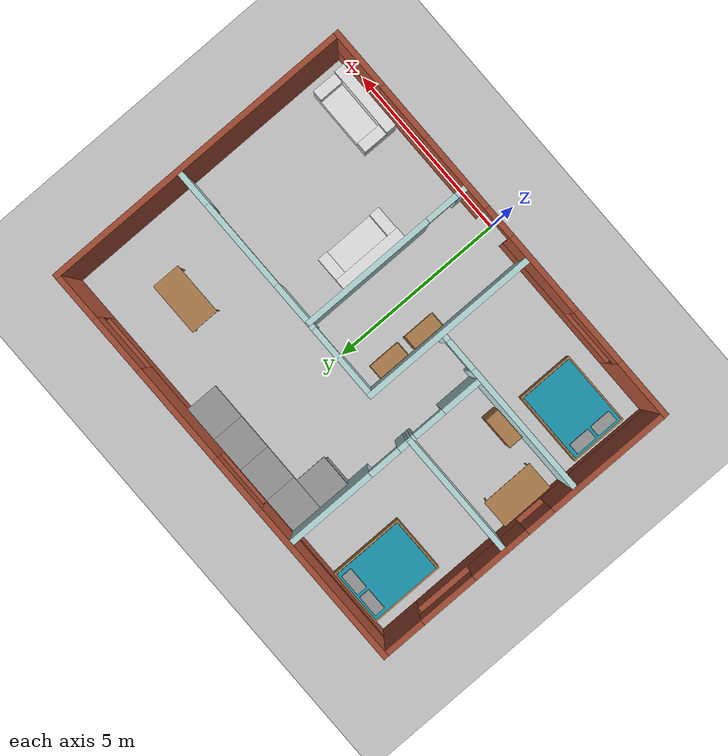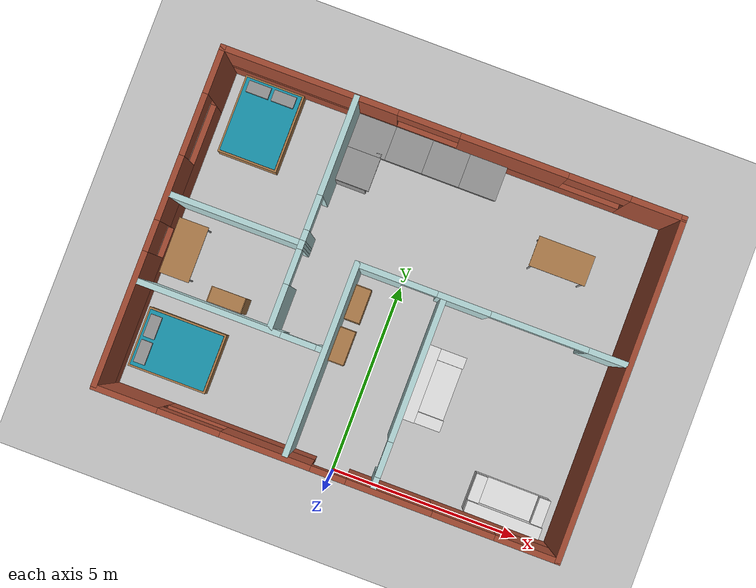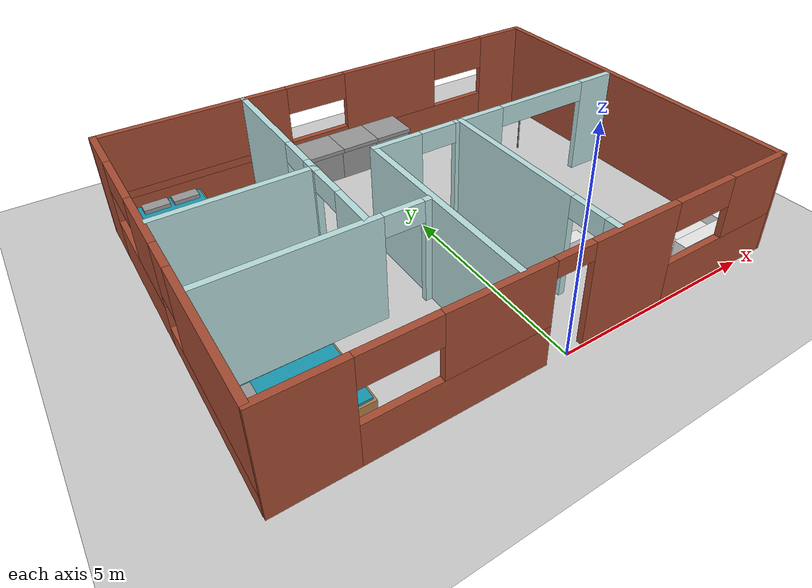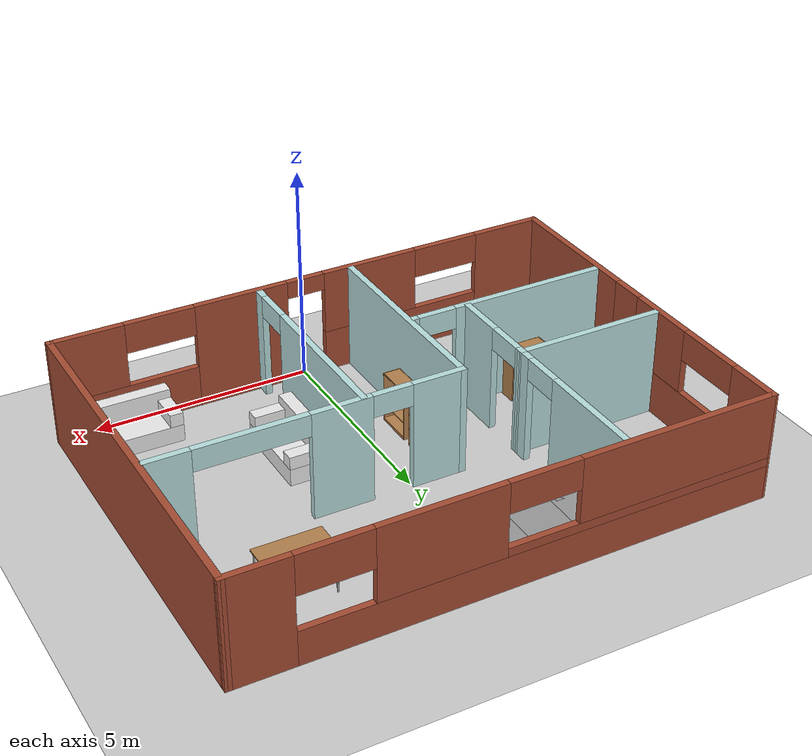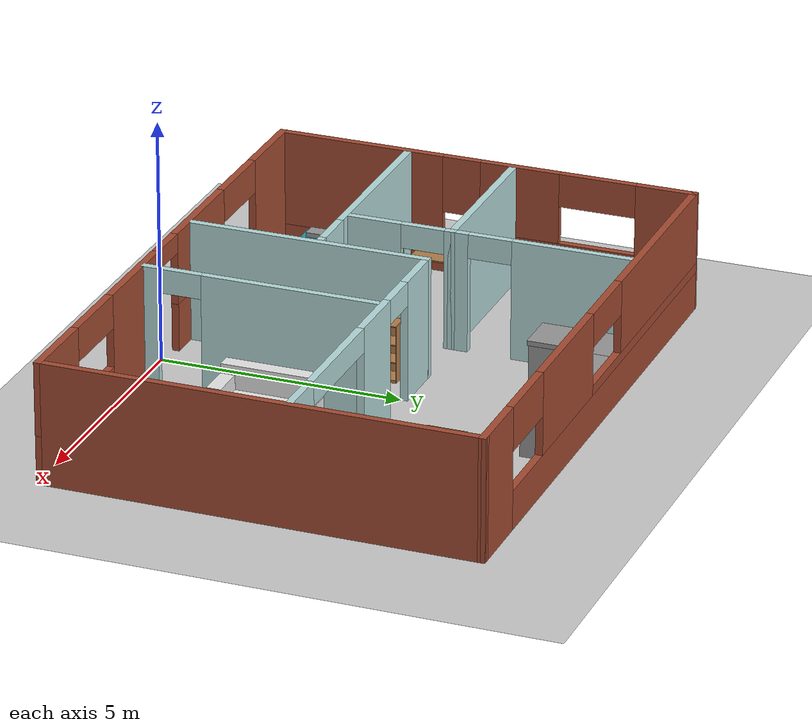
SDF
<sdf version="1.6">
 <world name="default">
  <plugin name="hello" filename="libhello.so"/>
  <light name="sun" type="directional">
   <pose>0 0 10 0 -0 0</pose>
   <diffuse>0.8 0.8 0.8 1</diffuse>
   <specular>0.2 0.2 0.2 1</specular>
   <attenuation>
    <range>1000</range>
    <constant>0.9</constant>
    <linear>0.01</linear>
    <quadratic>0.001</quadratic>
   </attenuation>
   <direction>-0.5 0.1 -0.9</direction>
  </light>
  <model name="ground_plane">
   <static>1</static>
   <link name="link">
    <collision name="collision">
     <geometry><plane><normal>0 0 1</normal><size>100 100</size></plane></geometry>
     <surface><friction><ode><mu>100</mu><mu2>50</mu2></ode></friction></surface>
    </collision>
    <visual name="visual">
     <cast_shadows>0</cast_shadows>
     <geometry><plane><normal>0 0 1</normal><size>100 100</size></plane></geometry>
     <material>
      <script><uri>file://media/materials/scripts/gazebo.material</uri><name>Gazebo/Grey</name></script>
     </material>
    </visual>
   </link>
  </model>
  <gravity>0 0 -9.8</gravity>
  <magnetic_field>6e-06 2.3e-05 -4.2e-05</magnetic_field>
  <atmosphere type="adiabatic"/>
  <physics name="default_physics" default="0" type="ode">
   <max_step_size>0.001</max_step_size>
   <real_time_factor>1</real_time_factor>
   <real_time_update_rate>1000</real_time_update_rate>
  </physics>
  <scene><ambient>0.4 0.4 0.4 1</ambient><background>0.7 0.7 0.7 1</background><shadows>1</shadows></scene>
  <spherical_coordinates>
   <surface_model>EARTH_WGS84</surface_model>
   <latitude_deg>0</latitude_deg>
   <longitude_deg>0</longitude_deg>
   <elevation>0</elevation>
   <heading_deg>0</heading_deg>
  </spherical_coordinates>
  <model name="myhouse">
   <pose>-0.11281 4.46423 0 0 -0 0</pose>
   <link name="Wall_116">
    <pose>1.19186 -1.85654 0 0 0 -1.5708</pose>
    <visual name="Wall_116_Visual_0">
     <pose>-0.621483 0 1.25 0 -0 0</pose>
     <geometry><box><size>3.75703 0.15 2.5</size></box></geometry>
     <material>
      <script><uri>file://media/materials/scripts/gazebo.material</uri><name>Gazebo/Grey</name></script>
      <ambient>0.721569 0.866667 0.866667 1</ambient>
     </material>
     <meta><layer>0</layer></meta>
    </visual>
    <collision name="Wall_116_Collision_0">
     <geometry><box><size>3.75703 0.15 2.5</size></box></geometry>
     <pose>-0.621483 0 1.25 0 -0 0</pose>
    </collision>
    <visual name="Wall_116_Visual_1">
     <pose>2.32852 0 1.25 0 -0 0</pose>
     <geometry><box><size>0.342966 0.15 2.5</size></box></geometry>
     <material>
      <script><uri>file://media/materials/scripts/gazebo.material</uri><name>Gazebo/Grey</name></script>
      <ambient>0.721569 0.866667 0.866667 1</ambient>
     </material>
     <meta><layer>0</layer></meta>
    </visual>
    <collision name="Wall_116_Collision_1">
     <geometry><box><size>0.342966 0.15 2.5</size></box></geometry>
     <pose>2.32852 0 1.25 0 -0 0</pose>
    </collision>
    <visual name="Wall_116_Visual_2">
     <pose>1.70703 0 2.25 0 -0 0</pose>
     <geometry><box><size>0.9 0.15 0.5</size></box></geometry>
     <material>
      <script><uri>file://media/materials/scripts/gazebo.material</uri><name>Gazebo/Grey</name></script>
      <ambient>0.721569 0.866667 0.866667 1</ambient>
     </material>
     <meta><layer>0</layer></meta>
    </visual>
    <collision name="Wall_116_Collision_2">
     <geometry><box><size>0.9 0.15 0.5</size></box></geometry>
     <pose>1.70703 0 2.25 0 -0 0</pose>
    </collision>
   </link>
   <link name="Wall_124">
    <pose>0 -4.37502 0 0 -0 0</pose>
    <visual name="Wall_124_Visual_0">
     <pose>-5.15314 0 1.25 0 -0 0</pose>
     <geometry><box><size>1.69372 0.15 2.5</size></box></geometry>
     <material>
      <script><uri>file://media/materials/scripts/gazebo.material</uri><name>Gazebo/Bricks</name></script>
      <ambient>1 1 1 1</ambient>
     </material>
     <meta><layer>0</layer></meta>
    </visual>
    <collision name="Wall_124_Collision_0">
     <geometry><box><size>1.69372 0.15 2.5</size></box></geometry>
     <pose>-5.15314 0 1.25 0 -0 0</pose>
    </collision>
    <visual name="Wall_124_Visual_1">
     <pose>1.60947 0 1.25 0 -0 0</pose>
     <geometry><box><size>2.19554 0.15 2.5</size></box></geometry>
     <material>
      <script><uri>file://media/materials/scripts/gazebo.material</uri><name>Gazebo/Bricks</name></script>
      <ambient>1 1 1 1</ambient>
     </material>
     <meta><layer>0</layer></meta>
    </visual>
    <collision name="Wall_124_Collision_1">
     <geometry><box><size>2.19554 0.15 2.5</size></box></geometry>
     <pose>1.60947 0 1.25 0 -0 0</pose>
    </collision>
    <visual name="Wall_124_Visual_2">
     <pose>-2.34729 0 0.5 0 -0 0</pose>
     <geometry><box><size>3.91797 0.15 1</size></box></geometry>
     <material>
      <script><uri>file://media/materials/scripts/gazebo.material</uri><name>Gazebo/Bricks</name></script>
      <ambient>1 1 1 1</ambient>
     </material>
     <meta><layer>0</layer></meta>
    </visual>
    <collision name="Wall_124_Collision_2">
     <geometry><box><size>3.91797 0.15 1</size></box></geometry>
     <pose>-2.34729 0 0.5 0 -0 0</pose>
    </collision>
    <visual name="Wall_124_Visual_3">
     <pose>4.35362 0 0.5 0 -0 0</pose>
     <geometry><box><size>3.29276 0.15 1</size></box></geometry>
     <material>
      <script><uri>file://media/materials/scripts/gazebo.material</uri><name>Gazebo/Bricks</name></script>
      <ambient>1 1 1 1</ambient>
     </material>
     <meta><layer>0</layer></meta>
    </visual>
    <collision name="Wall_124_Collision_3">
     <geometry><box><size>3.29276 0.15 1</size></box></geometry>
     <pose>4.35362 0 0.5 0 -0 0</pose>
    </collision>
    <visual name="Wall_124_Visual_4">
     <pose>-1.54729 0 1.75 0 -0 0</pose>
     <geometry><box><size>2.31797 0.15 1.5</size></box></geometry>
     <material>
      <script><uri>file://media/materials/scripts/gazebo.material</uri><name>Gazebo/Bricks</name></script>
      <ambient>1 1 1 1</ambient>
     </material>
     <meta><layer>0</layer></meta>
    </visual>
    <collision name="Wall_124_Collision_4">
     <geometry><box><size>2.31797 0.15 1.5</size></box></geometry>
     <pose>-1.54729 0 1.75 0 -0 0</pose>
    </collision>
    <visual name="Wall_124_Visual_5">
     <pose>-1.54729 0 1.75 0 -0 0</pose>
     <geometry><box><size>2.31797 0.15 1.5</size></box></geometry>
     <material>
      <script><uri>file://media/materials/scripts/gazebo.material</uri><name>Gazebo/Bricks</name></script>
      <ambient>1 1 1 1</ambient>
     </material>
     <meta><layer>0</layer></meta>
    </visual>
    <collision name="Wall_124_Collision_5">
     <geometry><box><size>2.31797 0.15 1.5</size></box></geometry>
     <pose>-1.54729 0 1.75 0 -0 0</pose>
    </collision>
    <visual name="Wall_124_Visual_6">
     <pose>5.15362 0 1.75 0 -0 0</pose>
     <geometry><box><size>1.69276 0.15 1.5</size></box></geometry>
     <material>
      <script><uri>file://media/materials/scripts/gazebo.material</uri><name>Gazebo/Bricks</name></script>
      <ambient>1 1 1 1</ambient>
     </material>
     <meta><layer>0</layer></meta>
    </visual>
    <collision name="Wall_124_Collision_6">
     <geometry><box><size>1.69276 0.15 1.5</size></box></geometry>
     <pose>5.15362 0 1.75 0 -0 0</pose>
    </collision>
    <visual name="Wall_124_Visual_7">
     <pose>-3.50628 0 2.15 0 -0 0</pose>
     <geometry><box><size>1.6 0.15 0.7</size></box></geometry>
     <material>
      <script><uri>file://media/materials/scripts/gazebo.material</uri><name>Gazebo/Bricks</name></script>
      <ambient>1 1 1 1</ambient>
     </material>
     <meta><layer>0</layer></meta>
    </visual>
    <collision name="Wall_124_Collision_7">
     <geometry><box><size>1.6 0.15 0.7</size></box></geometry>
     <pose>-3.50628 0 2.15 0 -0 0</pose>
    </collision>
    <visual name="Wall_124_Visual_8">
     <pose>3.50724 0 2.15 0 -0 0</pose>
     <geometry><box><size>1.6 0.15 0.7</size></box></geometry>
     <material>
      <script><uri>file://media/materials/scripts/gazebo.material</uri><name>Gazebo/Bricks</name></script>
      <ambient>1 1 1 1</ambient>
     </material>
     <meta><layer>0</layer></meta>
    </visual>
    <collision name="Wall_124_Collision_8">
     <geometry><box><size>1.6 0.15 0.7</size></box></geometry>
     <pose>3.50724 0 2.15 0 -0 0</pose>
    </collision>
    <visual name="Wall_124_Visual_9">
     <pose>0.061697 0 2.3 0 -0 0</pose>
     <geometry><box><size>0.9 0.15 0.4</size></box></geometry>
     <material>
      <script><uri>file://media/materials/scripts/gazebo.material</uri><name>Gazebo/Bricks</name></script>
      <ambient>1 1 1 1</ambient>
     </material>
     <meta><layer>0</layer></meta>
    </visual>
    <collision name="Wall_124_Collision_9">
     <geometry><box><size>0.9 0.15 0.4</size></box></geometry>
     <pose>0.061697 0 2.3 0 -0 0</pose>
    </collision>
    <visual name="Wall_124_Visual_10">
     <pose>0.061697 0 2.3 0 -0 0</pose>
     <geometry><box><size>0.9 0.15 0.4</size></box></geometry>
     <material>
      <script><uri>file://media/materials/scripts/gazebo.material</uri><name>Gazebo/Bricks</name></script>
      <ambient>1 1 1 1</ambient>
     </material>
     <meta><layer>0</layer></meta>
    </visual>
    <collision name="Wall_124_Collision_10">
     <geometry><box><size>0.9 0.15 0.4</size></box></geometry>
     <pose>0.061697 0 2.3 0 -0 0</pose>
    </collision>
   </link>
   <link name="Wall_125">
    <collision name="Wall_125_Collision">
     <geometry><box><size>8.9 0.15 2.5</size></box></geometry>
     <pose>0 0 1.25 0 -0 0</pose>
    </collision>
    <visual name="Wall_125_Visual">
     <pose>0 0 1.25 0 -0 0</pose>
     <geometry><box><size>8.9 0.15 2.5</size></box></geometry>
     <material>
      <script><uri>file://media/materials/scripts/gazebo.material</uri><name>Gazebo/Bricks</name></script>
      <ambient>1 1 1 1</ambient>
     </material>
     <meta><layer>0</layer></meta>
    </visual>
    <pose>5.9275 -2e-05 0 0 -0 1.57022</pose>
   </link>
   <link name="Wall_126">
    <pose>0 4.36848 0 0 0 -3.1405</pose>
    <visual name="Wall_126_Visual_0">
     <pose>-5.28653 0 1.25 0 -0 0</pose>
     <geometry><box><size>1.43694 0.15 2.5</size></box></geometry>
     <material>
      <script><uri>file://media/materials/scripts/gazebo.material</uri><name>Gazebo/Bricks</name></script>
      <ambient>1 1 1 1</ambient>
     </material>
     <meta><layer>0</layer></meta>
    </visual>
    <collision name="Wall_126_Collision_0">
     <geometry><box><size>1.43694 0.15 2.5</size></box></geometry>
     <pose>-5.28653 0 1.25 0 -0 0</pose>
    </collision>
    <visual name="Wall_126_Visual_1">
     <pose>0.718468 0 0.4 0 -0 0</pose>
     <geometry><box><size>10.5731 0.15 0.8</size></box></geometry>
     <material>
      <script><uri>file://media/materials/scripts/gazebo.material</uri><name>Gazebo/Bricks</name></script>
      <ambient>1 1 1 1</ambient>
     </material>
     <meta><layer>0</layer></meta>
    </visual>
    <collision name="Wall_126_Collision_1">
     <geometry><box><size>10.5731 0.15 0.8</size></box></geometry>
     <pose>0.718468 0 0.4 0 -0 0</pose>
    </collision>
    <visual name="Wall_126_Visual_2">
     <pose>-1.57991 0 1.65 0 -0 0</pose>
     <geometry><box><size>2.77631 0.15 1.7</size></box></geometry>
     <material>
      <script><uri>file://media/materials/scripts/gazebo.material</uri><name>Gazebo/Bricks</name></script>
      <ambient>1 1 1 1</ambient>
     </material>
     <meta><layer>0</layer></meta>
    </visual>
    <collision name="Wall_126_Collision_2">
     <geometry><box><size>2.77631 0.15 1.7</size></box></geometry>
     <pose>-1.57991 0 1.65 0 -0 0</pose>
    </collision>
    <visual name="Wall_126_Visual_3">
     <pose>2.90663 0 0.9 0 -0 0</pose>
     <geometry><box><size>6.19676 0.15 0.2</size></box></geometry>
     <material>
      <script><uri>file://media/materials/scripts/gazebo.material</uri><name>Gazebo/Bricks</name></script>
      <ambient>1 1 1 1</ambient>
     </material>
     <meta><layer>0</layer></meta>
    </visual>
    <collision name="Wall_126_Collision_3">
     <geometry><box><size>6.19676 0.15 0.2</size></box></geometry>
     <pose>2.90663 0 0.9 0 -0 0</pose>
    </collision>
    <visual name="Wall_126_Visual_4">
     <pose>3.70662 0 1.75 0 -0 0</pose>
     <geometry><box><size>4.59676 0.15 1.5</size></box></geometry>
     <material>
      <script><uri>file://media/materials/scripts/gazebo.material</uri><name>Gazebo/Bricks</name></script>
      <ambient>1 1 1 1</ambient>
     </material>
     <meta><layer>0</layer></meta>
    </visual>
    <collision name="Wall_126_Collision_4">
     <geometry><box><size>4.59676 0.15 1.5</size></box></geometry>
     <pose>3.70662 0 1.75 0 -0 0</pose>
    </collision>
    <visual name="Wall_126_Visual_5">
     <pose>-3.76807 0 2.05 0 -0 0</pose>
     <geometry><box><size>1.6 0.15 0.9</size></box></geometry>
     <material>
      <script><uri>file://media/materials/scripts/gazebo.material</uri><name>Gazebo/Bricks</name></script>
      <ambient>1 1 1 1</ambient>
     </material>
     <meta><layer>0</layer></meta>
    </visual>
    <collision name="Wall_126_Collision_5">
     <geometry><box><size>1.6 0.15 0.9</size></box></geometry>
     <pose>-3.76807 0 2.05 0 -0 0</pose>
    </collision>
    <visual name="Wall_126_Visual_6">
     <pose>0.608246 0 2.15 0 -0 0</pose>
     <geometry><box><size>1.6 0.15 0.7</size></box></geometry>
     <material>
      <script><uri>file://media/materials/scripts/gazebo.material</uri><name>Gazebo/Bricks</name></script>
      <ambient>1 1 1 1</ambient>
     </material>
     <meta><layer>0</layer></meta>
    </visual>
    <collision name="Wall_126_Collision_6">
     <geometry><box><size>1.6 0.15 0.7</size></box></geometry>
     <pose>0.608246 0 2.15 0 -0 0</pose>
    </collision>
   </link>
   <link name="Wall_127">
    <pose>-5.93 0.02998 0 0 0 -1.5708</pose>
    <visual name="Wall_127_Visual_0">
     <pose>-3.77443 0 1.25 0 -0 0</pose>
     <geometry><box><size>1.26514 0.15 2.5</size></box></geometry>
     <material>
      <script><uri>file://media/materials/scripts/gazebo.material</uri><name>Gazebo/Bricks</name></script>
      <ambient>1 1 1 1</ambient>
     </material>
     <meta><layer>0</layer></meta>
    </visual>
    <collision name="Wall_127_Collision_0">
     <geometry><box><size>1.26514 0.15 2.5</size></box></geometry>
     <pose>-3.77443 0 1.25 0 -0 0</pose>
    </collision>
    <visual name="Wall_127_Visual_1">
     <pose>-1.50767 0 0.5 0 -0 0</pose>
     <geometry><box><size>3.26837 0.15 1</size></box></geometry>
     <material>
      <script><uri>file://media/materials/scripts/gazebo.material</uri><name>Gazebo/Bricks</name></script>
      <ambient>1 1 1 1</ambient>
     </material>
     <meta><layer>0</layer></meta>
    </visual>
    <collision name="Wall_127_Collision_1">
     <geometry><box><size>3.26837 0.15 1</size></box></geometry>
     <pose>-1.50767 0 0.5 0 -0 0</pose>
    </collision>
    <visual name="Wall_127_Visual_2">
     <pose>2.26676 0 0.25 0 -0 0</pose>
     <geometry><box><size>4.28049 0.15 0.5</size></box></geometry>
     <material>
      <script><uri>file://media/materials/scripts/gazebo.material</uri><name>Gazebo/Bricks</name></script>
      <ambient>1 1 1 1</ambient>
     </material>
     <meta><layer>0</layer></meta>
    </visual>
    <collision name="Wall_127_Collision_2">
     <geometry><box><size>4.28049 0.15 0.5</size></box></geometry>
     <pose>2.26676 0 0.25 0 -0 0</pose>
    </collision>
    <visual name="Wall_127_Visual_3">
     <pose>2.66676 0 1.5 0 -0 0</pose>
     <geometry><box><size>3.48049 0.15 2</size></box></geometry>
     <material>
      <script><uri>file://media/materials/scripts/gazebo.material</uri><name>Gazebo/Bricks</name></script>
      <ambient>1 1 1 1</ambient>
     </material>
     <meta><layer>0</layer></meta>
    </visual>
    <collision name="Wall_127_Collision_3">
     <geometry><box><size>3.48049 0.15 2</size></box></geometry>
     <pose>2.66676 0 1.5 0 -0 0</pose>
    </collision>
    <visual name="Wall_127_Visual_4">
     <pose>-0.707673 0 1.75 0 -0 0</pose>
     <geometry><box><size>1.66837 0.15 1.5</size></box></geometry>
     <material>
      <script><uri>file://media/materials/scripts/gazebo.material</uri><name>Gazebo/Bricks</name></script>
      <ambient>1 1 1 1</ambient>
     </material>
     <meta><layer>0</layer></meta>
    </visual>
    <collision name="Wall_127_Collision_4">
     <geometry><box><size>1.66837 0.15 1.5</size></box></geometry>
     <pose>-0.707673 0 1.75 0 -0 0</pose>
    </collision>
    <visual name="Wall_127_Visual_5">
     <pose>0.526513 0 1.9 0 -0 0</pose>
     <geometry><box><size>0.8 0.15 1.2</size></box></geometry>
     <material>
      <script><uri>file://media/materials/scripts/gazebo.material</uri><name>Gazebo/Bricks</name></script>
      <ambient>1 1 1 1</ambient>
     </material>
     <meta><layer>0</layer></meta>
    </visual>
    <collision name="Wall_127_Collision_5">
     <geometry><box><size>0.8 0.15 1.2</size></box></geometry>
     <pose>0.526513 0 1.9 0 -0 0</pose>
    </collision>
    <visual name="Wall_127_Visual_6">
     <pose>-2.34186 0 2.15 0 -0 0</pose>
     <geometry><box><size>1.6 0.15 0.7</size></box></geometry>
     <material>
      <script><uri>file://media/materials/scripts/gazebo.material</uri><name>Gazebo/Bricks</name></script>
      <ambient>1 1 1 1</ambient>
     </material>
     <meta><layer>0</layer></meta>
    </visual>
    <collision name="Wall_127_Collision_6">
     <geometry><box><size>1.6 0.15 0.7</size></box></geometry>
     <pose>-2.34186 0 2.15 0 -0 0</pose>
    </collision>
   </link>
   <link name="Wall_129">
    <collision name="Wall_129_Collision">
     <geometry><box><size>5 0.15 2.5</size></box></geometry>
     <pose>0 0 1.25 0 -0 0</pose>
    </collision>
    <visual name="Wall_129_Visual">
     <pose>0 0 1.25 0 -0 0</pose>
     <geometry><box><size>5 0.15 2.5</size></box></geometry>
     <material>
      <script><uri>file://media/materials/scripts/gazebo.material</uri><name>Gazebo/Grey</name></script>
      <ambient>0.721569 0.866667 0.866667 1</ambient>
     </material>
     <meta><layer>0</layer></meta>
    </visual>
    <pose>-1.05639 -1.82996 0 0 -0 1.5708</pose>
   </link>
   <link name="Wall_139">
    <pose>2.37537 0.594546 0 0 -0 0</pose>
    <visual name="Wall_139_Visual_0">
     <pose>-2.88296 0 1.25 0 -0 0</pose>
     <geometry><box><size>1.23409 0.15 2.5</size></box></geometry>
     <material>
      <script><uri>file://media/materials/scripts/gazebo.material</uri><name>Gazebo/Grey</name></script>
      <ambient>0.721569 0.866667 0.866667 1</ambient>
     </material>
     <meta><layer>0</layer></meta>
    </visual>
    <collision name="Wall_139_Collision_0">
     <geometry><box><size>1.23409 0.15 2.5</size></box></geometry>
     <pose>-2.88296 0 1.25 0 -0 0</pose>
    </collision>
    <visual name="Wall_139_Visual_1">
     <pose>-0.682749 0 1.25 0 -0 0</pose>
     <geometry><box><size>1.36633 0.15 2.5</size></box></geometry>
     <material>
      <script><uri>file://media/materials/scripts/gazebo.material</uri><name>Gazebo/Grey</name></script>
      <ambient>0.721569 0.866667 0.866667 1</ambient>
     </material>
     <meta><layer>0</layer></meta>
    </visual>
    <collision name="Wall_139_Collision_1">
     <geometry><box><size>1.36633 0.15 2.5</size></box></geometry>
     <pose>-0.682749 0 1.25 0 -0 0</pose>
    </collision>
    <visual name="Wall_139_Visual_2">
     <pose>3.00021 0 1.25 0 -0 0</pose>
     <geometry><box><size>0.999584 0.15 2.5</size></box></geometry>
     <material>
      <script><uri>file://media/materials/scripts/gazebo.material</uri><name>Gazebo/Grey</name></script>
      <ambient>0.721569 0.866667 0.866667 1</ambient>
     </material>
     <meta><layer>0</layer></meta>
    </visual>
    <collision name="Wall_139_Collision_2">
     <geometry><box><size>0.999584 0.15 2.5</size></box></geometry>
     <pose>3.00021 0 1.25 0 -0 0</pose>
    </collision>
    <visual name="Wall_139_Visual_3">
     <pose>-1.81591 0 2.25 0 -0 0</pose>
     <geometry><box><size>0.9 0.15 0.5</size></box></geometry>
     <material>
      <script><uri>file://media/materials/scripts/gazebo.material</uri><name>Gazebo/Grey</name></script>
      <ambient>0.721569 0.866667 0.866667 1</ambient>
     </material>
     <meta><layer>0</layer></meta>
    </visual>
    <collision name="Wall_139_Collision_3">
     <geometry><box><size>0.9 0.15 0.5</size></box></geometry>
     <pose>-1.81591 0 2.25 0 -0 0</pose>
    </collision>
    <visual name="Wall_139_Visual_4">
     <pose>1.25042 0 2.25 0 -0 0</pose>
     <geometry><box><size>2.5 0.15 0.5</size></box></geometry>
     <material>
      <script><uri>file://media/materials/scripts/gazebo.material</uri><name>Gazebo/Grey</name></script>
      <ambient>0.721569 0.866667 0.866667 1</ambient>
     </material>
     <meta><layer>0</layer></meta>
    </visual>
    <collision name="Wall_139_Collision_4">
     <geometry><box><size>2.5 0.15 0.5</size></box></geometry>
     <pose>1.25042 0 2.25 0 -0 0</pose>
    </collision>
   </link>
   <link name="Wall_154">
    <pose>-3.48298 -1.6348 0 0 -0 0</pose>
    <visual name="Wall_154_Visual_0">
     <pose>-0.535862 0 1.25 0 -0 0</pose>
     <geometry><box><size>3.67828 0.15 2.5</size></box></geometry>
     <material>
      <script><uri>file://media/materials/scripts/gazebo.material</uri><name>Gazebo/Grey</name></script>
      <ambient>0.721569 0.866667 0.866667 1</ambient>
     </material>
     <meta><layer>0</layer></meta>
    </visual>
    <collision name="Wall_154_Collision_0">
     <geometry><box><size>3.67828 0.15 2.5</size></box></geometry>
     <pose>-0.535862 0 1.25 0 -0 0</pose>
    </collision>
    <visual name="Wall_154_Visual_1">
     <pose>2.28914 0 1.25 0 -0 0</pose>
     <geometry><box><size>0.171723 0.15 2.5</size></box></geometry>
     <material>
      <script><uri>file://media/materials/scripts/gazebo.material</uri><name>Gazebo/Grey</name></script>
      <ambient>0.721569 0.866667 0.866667 1</ambient>
     </material>
     <meta><layer>0</layer></meta>
    </visual>
    <collision name="Wall_154_Collision_1">
     <geometry><box><size>0.171723 0.15 2.5</size></box></geometry>
     <pose>2.28914 0 1.25 0 -0 0</pose>
    </collision>
    <visual name="Wall_154_Visual_2">
     <pose>1.75328 0 2.25 0 -0 0</pose>
     <geometry><box><size>0.9 0.15 0.5</size></box></geometry>
     <material>
      <script><uri>file://media/materials/scripts/gazebo.material</uri><name>Gazebo/Grey</name></script>
      <ambient>0.721569 0.866667 0.866667 1</ambient>
     </material>
     <meta><layer>0</layer></meta>
    </visual>
    <collision name="Wall_154_Collision_2">
     <geometry><box><size>0.9 0.15 0.5</size></box></geometry>
     <pose>1.75328 0 2.25 0 -0 0</pose>
    </collision>
   </link>
   <link name="Wall_157">
    <collision name="Wall_157_Collision">
     <geometry><box><size>3.48493 0.15 2.5</size></box></geometry>
     <pose>0 0 1.25 0 -0 0</pose>
    </collision>
    <visual name="Wall_157_Visual">
     <pose>0 0 1.25 0 -0 0</pose>
     <geometry><box><size>3.48493 0.15 2.5</size></box></geometry>
     <material>
      <script><uri>file://media/materials/scripts/gazebo.material</uri><name>Gazebo/Grey</name></script>
      <ambient>0.721569 0.866667 0.866667 1</ambient>
     </material>
     <meta><layer>0</layer></meta>
    </visual>
    <pose>-4.14746 0.597189 0 0 -0 3.14147</pose>
   </link>
   <link name="Wall_160">
    <pose>-2.48 2.47198 0 0 -0 1.5708</pose>
    <visual name="Wall_160_Visual_0">
     <pose>-1.74137 0 1.25 0 -0 0</pose>
     <geometry><box><size>0.417261 0.15 2.5</size></box></geometry>
     <material>
      <script><uri>file://media/materials/scripts/gazebo.material</uri><name>Gazebo/Grey</name></script>
      <ambient>0.721569 0.866667 0.866667 1</ambient>
     </material>
     <meta><layer>0</layer></meta>
    </visual>
    <collision name="Wall_160_Collision_0">
     <geometry><box><size>0.417261 0.15 2.5</size></box></geometry>
     <pose>-1.74137 0 1.25 0 -0 0</pose>
    </collision>
    <visual name="Wall_160_Visual_1">
     <pose>0.65863 0 1.25 0 -0 0</pose>
     <geometry><box><size>2.58274 0.15 2.5</size></box></geometry>
     <material>
      <script><uri>file://media/materials/scripts/gazebo.material</uri><name>Gazebo/Grey</name></script>
      <ambient>0.721569 0.866667 0.866667 1</ambient>
     </material>
     <meta><layer>0</layer></meta>
    </visual>
    <collision name="Wall_160_Collision_1">
     <geometry><box><size>2.58274 0.15 2.5</size></box></geometry>
     <pose>0.65863 0 1.25 0 -0 0</pose>
    </collision>
    <visual name="Wall_160_Visual_2">
     <pose>-1.08274 0 2.25 0 -0 0</pose>
     <geometry><box><size>0.9 0.15 0.5</size></box></geometry>
     <material>
      <script><uri>file://media/materials/scripts/gazebo.material</uri><name>Gazebo/Grey</name></script>
      <ambient>0.721569 0.866667 0.866667 1</ambient>
     </material>
     <meta><layer>0</layer></meta>
    </visual>
    <collision name="Wall_160_Collision_2">
     <geometry><box><size>0.9 0.15 0.5</size></box></geometry>
     <pose>-1.08274 0 2.25 0 -0 0</pose>
    </collision>
   </link>
   <link name="Wall_162">
    <pose>-2.48 -0.47802 0 0 0 -1.5708</pose>
    <visual name="Wall_162_Visual_0">
     <pose>-1.03704 0 1.25 0 -0 0</pose>
     <geometry><box><size>0.225923 0.15 2.5</size></box></geometry>
     <material>
      <script><uri>file://media/materials/scripts/gazebo.material</uri><name>Gazebo/Grey</name></script>
      <ambient>0.721569 0.866667 0.866667 1</ambient>
     </material>
     <meta><layer>0</layer></meta>
    </visual>
    <collision name="Wall_162_Collision_0">
     <geometry><box><size>0.225923 0.15 2.5</size></box></geometry>
     <pose>-1.03704 0 1.25 0 -0 0</pose>
    </collision>
    <visual name="Wall_162_Visual_1">
     <pose>0.562961 0 1.25 0 -0 0</pose>
     <geometry><box><size>1.17408 0.15 2.5</size></box></geometry>
     <material>
      <script><uri>file://media/materials/scripts/gazebo.material</uri><name>Gazebo/Grey</name></script>
      <ambient>0.721569 0.866667 0.866667 1</ambient>
     </material>
     <meta><layer>0</layer></meta>
    </visual>
    <collision name="Wall_162_Collision_1">
     <geometry><box><size>1.17408 0.15 2.5</size></box></geometry>
     <pose>0.562961 0 1.25 0 -0 0</pose>
    </collision>
    <visual name="Wall_162_Visual_2">
     <pose>-0.474077 0 2.25 0 -0 0</pose>
     <geometry><box><size>0.9 0.15 0.5</size></box></geometry>
     <material>
      <script><uri>file://media/materials/scripts/gazebo.material</uri><name>Gazebo/Grey</name></script>
      <ambient>0.721569 0.866667 0.866667 1</ambient>
     </material>
     <meta><layer>0</layer></meta>
    </visual>
    <collision name="Wall_162_Collision_2">
     <geometry><box><size>0.9 0.15 0.5</size></box></geometry>
     <pose>-0.474077 0 2.25 0 -0 0</pose>
    </collision>
   </link>
   <static>1</static>
  </model>
  <model name="countertop">
   <link name="link_0">
    <pose>-0.025 0 -0.225 0 -0 0</pose>
    <inertial>
     <mass>1</mass>
     <inertia>
      <ixx>0.166667</ixx>
      <ixy>0</ixy>
      <ixz>0</ixz>
      <iyy>0.166667</iyy>
      <iyz>0</iyz>
      <izz>0.166667</izz>
     </inertia>
    </inertial>
    <visual name="visual">
     <geometry><box><size>0.8 1 0.8</size></box></geometry>
     <material>
      <lighting>1</lighting>
      <script><uri>file://media/materials/scripts/gazebo.material</uri><name>Gazebo/Grey</name></script>
      <shader type="pixel"><normal_map>__default__</normal_map></shader>
      <ambient>1 1 1 1</ambient>
      <diffuse>0.9 0.9 0.9 1</diffuse>
      <specular>0.01 0.01 0.01 1</specular>
      <emissive>0 0 0 1</emissive>
     </material>
    </visual>
    <collision name="collision">
     <geometry><box><size>0.8 1 0.8</size></box></geometry>
     <surface>
      <friction>
       <ode><mu>1</mu><mu2>1</mu2><fdir1>0 0 0</fdir1><slip1>0</slip1><slip2>0</slip2></ode>
       <torsional>
        <coefficient>1</coefficient>
        <patch_radius>0</patch_radius>
        <surface_radius>0</surface_radius>
        <use_patch_radius>1</use_patch_radius>
        <ode><slip>0</slip></ode>
       </torsional>
      </friction>
      <bounce><restitution_coefficient>0</restitution_coefficient><threshold>1e+06</threshold></bounce>
      <contact>
       <collide_without_contact>0</collide_without_contact>
       <collide_without_contact_bitmask>1</collide_without_contact_bitmask>
       <collide_bitmask>1</collide_bitmask>
       <ode>
        <soft_cfm>0</soft_cfm>
        <soft_erp>0.2</soft_erp>
        <kp>1e+13</kp>
        <kd>1</kd>
        <max_vel>0.01</max_vel>
        <min_depth>0</min_depth>
       </ode>
       <bullet>
        <split_impulse>1</split_impulse>
        <split_impulse_penetration_threshold>-0.01</split_impulse_penetration_threshold>
        <soft_cfm>0</soft_cfm>
        <soft_erp>0.2</soft_erp>
        <kp>1e+13</kp>
        <kd>1</kd>
       </bullet>
      </contact>
     </surface>
    </collision>
   </link>
   <link name="link_1">
    <pose>0.025 0 0.225 0 -0 0</pose>
    <inertial>
     <mass>1</mass>
     <inertia>
      <ixx>0.166667</ixx>
      <ixy>0</ixy>
      <ixz>0</ixz>
      <iyy>0.166667</iyy>
      <iyz>0</iyz>
      <izz>0.166667</izz>
     </inertia>
    </inertial>
    <visual name="visual">
     <geometry><box><size>0.9 1 0.1</size></box></geometry>
     <material>
      <lighting>1</lighting>
      <script><uri>file://media/materials/scripts/gazebo.material</uri><name>Gazebo/Grey</name></script>
      <shader type="pixel"><normal_map>__default__</normal_map></shader>
      <ambient>0.1 0.1 0.1 1</ambient>
      <diffuse>0.1 0.1 0.1 1</diffuse>
      <specular>0.01 0.01 0.01 1</specular>
      <emissive>0 0 0 1</emissive>
     </material>
    </visual>
    <collision name="collision">
     <geometry><box><size>0.9 1 0.1</size></box></geometry>
     <surface>
      <friction>
       <ode><mu>1</mu><mu2>1</mu2><fdir1>0 0 0</fdir1><slip1>0</slip1><slip2>0</slip2></ode>
       <torsional>
        <coefficient>1</coefficient>
        <patch_radius>0</patch_radius>
        <surface_radius>0</surface_radius>
        <use_patch_radius>1</use_patch_radius>
        <ode><slip>0</slip></ode>
       </torsional>
      </friction>
      <bounce><restitution_coefficient>0</restitution_coefficient><threshold>1e+06</threshold></bounce>
      <contact>
       <collide_without_contact>0</collide_without_contact>
       <collide_without_contact_bitmask>1</collide_without_contact_bitmask>
       <collide_bitmask>1</collide_bitmask>
       <ode>
        <soft_cfm>0</soft_cfm>
        <soft_erp>0.2</soft_erp>
        <kp>1e+13</kp>
        <kd>1</kd>
        <max_vel>0.01</max_vel>
        <min_depth>0</min_depth>
       </ode>
       <bullet>
        <split_impulse>1</split_impulse>
        <split_impulse_penetration_threshold>-0.01</split_impulse_penetration_threshold>
        <soft_cfm>0</soft_cfm>
        <soft_erp>0.2</soft_erp>
        <kp>1e+13</kp>
        <kd>1</kd>
       </bullet>
      </contact>
     </surface>
    </collision>
   </link>
   <joint name="link_0_JOINT_0" type="revolute">
    <parent>link_0</parent>
    <child>link_1</child>
    <axis>
     <xyz>1 0 0</xyz>
     <use_parent_model_frame>0</use_parent_model_frame>
     <limit>
      <lower>-1.79769e+308</lower>
      <upper>1.79769e+308</upper>
      <effort>-1</effort>
      <velocity>-1</velocity>
     </limit>
     <dynamics>
      <spring_reference>0</spring_reference>
      <spring_stiffness>0</spring_stiffness>
      <damping>0</damping>
      <friction>0</friction>
     </dynamics>
    </axis>
    <physics>
     <ode><limit><cfm>0</cfm><erp>0.2</erp></limit><suspension><cfm>0</cfm><erp>0.2</erp></suspension></ode>
    </physics>
   </joint>
   <static>1</static>
   <pose>-2.02123 8.33439 0.618131 0 0 -1.5707</pose>
  </model>
  <model name="countertop_clone">
   <link name="link_0">
    <pose>-0.025 0 -0.225 0 -0 0</pose>
    <inertial>
     <mass>1</mass>
     <inertia>
      <ixx>0.166667</ixx>
      <ixy>0</ixy>
      <ixz>0</ixz>
      <iyy>0.166667</iyy>
      <iyz>0</iyz>
      <izz>0.166667</izz>
     </inertia>
    </inertial>
    <visual name="visual">
     <geometry><box><size>0.8 1 0.8</size></box></geometry>
     <material>
      <lighting>1</lighting>
      <script><uri>file://media/materials/scripts/gazebo.material</uri><name>Gazebo/Grey</name></script>
      <shader type="pixel"><normal_map>__default__</normal_map></shader>
      <ambient>1 1 1 1</ambient>
      <diffuse>0.9 0.9 0.9 1</diffuse>
      <specular>0.01 0.01 0.01 1</specular>
      <emissive>0 0 0 1</emissive>
     </material>
    </visual>
    <collision name="collision">
     <geometry><box><size>0.8 1 0.8</size></box></geometry>
     <surface>
      <friction>
       <ode><mu>1</mu><mu2>1</mu2><fdir1>0 0 0</fdir1><slip1>0</slip1><slip2>0</slip2></ode>
       <torsional>
        <coefficient>1</coefficient>
        <patch_radius>0</patch_radius>
        <surface_radius>0</surface_radius>
        <use_patch_radius>1</use_patch_radius>
        <ode><slip>0</slip></ode>
       </torsional>
      </friction>
      <bounce><restitution_coefficient>0</restitution_coefficient><threshold>1e+06</threshold></bounce>
      <contact>
       <collide_without_contact>0</collide_without_contact>
       <collide_without_contact_bitmask>1</collide_without_contact_bitmask>
       <collide_bitmask>1</collide_bitmask>
       <ode>
        <soft_cfm>0</soft_cfm>
        <soft_erp>0.2</soft_erp>
        <kp>1e+13</kp>
        <kd>1</kd>
        <max_vel>0.01</max_vel>
        <min_depth>0</min_depth>
       </ode>
       <bullet>
        <split_impulse>1</split_impulse>
        <split_impulse_penetration_threshold>-0.01</split_impulse_penetration_threshold>
        <soft_cfm>0</soft_cfm>
        <soft_erp>0.2</soft_erp>
        <kp>1e+13</kp>
        <kd>1</kd>
       </bullet>
      </contact>
     </surface>
    </collision>
   </link>
   <link name="link_1">
    <pose>0.025 0 0.225 0 -0 0</pose>
    <inertial>
     <mass>1</mass>
     <inertia>
      <ixx>0.166667</ixx>
      <ixy>0</ixy>
      <ixz>0</ixz>
      <iyy>0.166667</iyy>
      <iyz>0</iyz>
      <izz>0.166667</izz>
     </inertia>
    </inertial>
    <visual name="visual">
     <geometry><box><size>0.9 1 0.1</size></box></geometry>
     <material>
      <lighting>1</lighting>
      <script><uri>file://media/materials/scripts/gazebo.material</uri><name>Gazebo/Grey</name></script>
      <shader type="pixel"><normal_map>__default__</normal_map></shader>
      <ambient>0.1 0.1 0.1 1</ambient>
      <diffuse>0.1 0.1 0.1 1</diffuse>
      <specular>0.01 0.01 0.01 1</specular>
      <emissive>0 0 0 1</emissive>
     </material>
    </visual>
    <collision name="collision">
     <geometry><box><size>0.9 1 0.1</size></box></geometry>
     <surface>
      <friction>
       <ode><mu>1</mu><mu2>1</mu2><fdir1>0 0 0</fdir1><slip1>0</slip1><slip2>0</slip2></ode>
       <torsional>
        <coefficient>1</coefficient>
        <patch_radius>0</patch_radius>
        <surface_radius>0</surface_radius>
        <use_patch_radius>1</use_patch_radius>
        <ode><slip>0</slip></ode>
       </torsional>
      </friction>
      <bounce><restitution_coefficient>0</restitution_coefficient><threshold>1e+06</threshold></bounce>
      <contact>
       <collide_without_contact>0</collide_without_contact>
       <collide_without_contact_bitmask>1</collide_without_contact_bitmask>
       <collide_bitmask>1</collide_bitmask>
       <ode>
        <soft_cfm>0</soft_cfm>
        <soft_erp>0.2</soft_erp>
        <kp>1e+13</kp>
        <kd>1</kd>
        <max_vel>0.01</max_vel>
        <min_depth>0</min_depth>
       </ode>
       <bullet>
        <split_impulse>1</split_impulse>
        <split_impulse_penetration_threshold>-0.01</split_impulse_penetration_threshold>
        <soft_cfm>0</soft_cfm>
        <soft_erp>0.2</soft_erp>
        <kp>1e+13</kp>
        <kd>1</kd>
       </bullet>
      </contact>
     </surface>
    </collision>
   </link>
   <joint name="link_0_JOINT_0" type="revolute">
    <parent>link_0</parent>
    <child>link_1</child>
    <axis>
     <xyz>1 0 0</xyz>
     <use_parent_model_frame>0</use_parent_model_frame>
     <limit>
      <lower>-1.79769e+308</lower>
      <upper>1.79769e+308</upper>
      <effort>-1</effort>
      <velocity>-1</velocity>
     </limit>
     <dynamics>
      <spring_reference>0</spring_reference>
      <spring_stiffness>0</spring_stiffness>
      <damping>0</damping>
      <friction>0</friction>
     </dynamics>
    </axis>
    <physics>
     <ode><limit><cfm>0</cfm><erp>0.2</erp></limit><suspension><cfm>0</cfm><erp>0.2</erp></suspension></ode>
    </physics>
   </joint>
   <static>1</static>
   <pose>-1.0217 8.3348 0.618131 0 0 -1.5707</pose>
  </model>
  <model name="countertop_clone_clone">
   <link name="link_0">
    <pose>-0.025 0 -0.225 0 -0 0</pose>
    <inertial>
     <mass>1</mass>
     <inertia>
      <ixx>0.166667</ixx>
      <ixy>0</ixy>
      <ixz>0</ixz>
      <iyy>0.166667</iyy>
      <iyz>0</iyz>
      <izz>0.166667</izz>
     </inertia>
    </inertial>
    <visual name="visual">
     <geometry><box><size>0.8 1 0.8</size></box></geometry>
     <material>
      <lighting>1</lighting>
      <script><uri>file://media/materials/scripts/gazebo.material</uri><name>Gazebo/Grey</name></script>
      <shader type="pixel"><normal_map>__default__</normal_map></shader>
      <ambient>1 1 1 1</ambient>
      <diffuse>0.9 0.9 0.9 1</diffuse>
      <specular>0.01 0.01 0.01 1</specular>
      <emissive>0 0 0 1</emissive>
     </material>
    </visual>
    <collision name="collision">
     <geometry><box><size>0.8 1 0.8</size></box></geometry>
     <surface>
      <friction>
       <ode><mu>1</mu><mu2>1</mu2><fdir1>0 0 0</fdir1><slip1>0</slip1><slip2>0</slip2></ode>
       <torsional>
        <coefficient>1</coefficient>
        <patch_radius>0</patch_radius>
        <surface_radius>0</surface_radius>
        <use_patch_radius>1</use_patch_radius>
        <ode><slip>0</slip></ode>
       </torsional>
      </friction>
      <bounce><restitution_coefficient>0</restitution_coefficient><threshold>1e+06</threshold></bounce>
      <contact>
       <collide_without_contact>0</collide_without_contact>
       <collide_without_contact_bitmask>1</collide_without_contact_bitmask>
       <collide_bitmask>1</collide_bitmask>
       <ode>
        <soft_cfm>0</soft_cfm>
        <soft_erp>0.2</soft_erp>
        <kp>1e+13</kp>
        <kd>1</kd>
        <max_vel>0.01</max_vel>
        <min_depth>0</min_depth>
       </ode>
       <bullet>
        <split_impulse>1</split_impulse>
        <split_impulse_penetration_threshold>-0.01</split_impulse_penetration_threshold>
        <soft_cfm>0</soft_cfm>
        <soft_erp>0.2</soft_erp>
        <kp>1e+13</kp>
        <kd>1</kd>
       </bullet>
      </contact>
     </surface>
    </collision>
   </link>
   <link name="link_1">
    <pose>0.025 0 0.225 0 -0 0</pose>
    <inertial>
     <mass>1</mass>
     <inertia>
      <ixx>0.166667</ixx>
      <ixy>0</ixy>
      <ixz>0</ixz>
      <iyy>0.166667</iyy>
      <iyz>0</iyz>
      <izz>0.166667</izz>
     </inertia>
    </inertial>
    <visual name="visual">
     <geometry><box><size>0.9 1 0.1</size></box></geometry>
     <material>
      <lighting>1</lighting>
      <script><uri>file://media/materials/scripts/gazebo.material</uri><name>Gazebo/Grey</name></script>
      <shader type="pixel"><normal_map>__default__</normal_map></shader>
      <ambient>0.1 0.1 0.1 1</ambient>
      <diffuse>0.1 0.1 0.1 1</diffuse>
      <specular>0.01 0.01 0.01 1</specular>
      <emissive>0 0 0 1</emissive>
     </material>
    </visual>
    <collision name="collision">
     <geometry><box><size>0.9 1 0.1</size></box></geometry>
     <surface>
      <friction>
       <ode><mu>1</mu><mu2>1</mu2><fdir1>0 0 0</fdir1><slip1>0</slip1><slip2>0</slip2></ode>
       <torsional>
        <coefficient>1</coefficient>
        <patch_radius>0</patch_radius>
        <surface_radius>0</surface_radius>
        <use_patch_radius>1</use_patch_radius>
        <ode><slip>0</slip></ode>
       </torsional>
      </friction>
      <bounce><restitution_coefficient>0</restitution_coefficient><threshold>1e+06</threshold></bounce>
      <contact>
       <collide_without_contact>0</collide_without_contact>
       <collide_without_contact_bitmask>1</collide_without_contact_bitmask>
       <collide_bitmask>1</collide_bitmask>
       <ode>
        <soft_cfm>0</soft_cfm>
        <soft_erp>0.2</soft_erp>
        <kp>1e+13</kp>
        <kd>1</kd>
        <max_vel>0.01</max_vel>
        <min_depth>0</min_depth>
       </ode>
       <bullet>
        <split_impulse>1</split_impulse>
        <split_impulse_penetration_threshold>-0.01</split_impulse_penetration_threshold>
        <soft_cfm>0</soft_cfm>
        <soft_erp>0.2</soft_erp>
        <kp>1e+13</kp>
        <kd>1</kd>
       </bullet>
      </contact>
     </surface>
    </collision>
   </link>
   <joint name="link_0_JOINT_0" type="revolute">
    <parent>link_0</parent>
    <child>link_1</child>
    <axis>
     <xyz>1 0 0</xyz>
     <use_parent_model_frame>0</use_parent_model_frame>
     <limit>
      <lower>-1.79769e+308</lower>
      <upper>1.79769e+308</upper>
      <effort>-1</effort>
      <velocity>-1</velocity>
     </limit>
     <dynamics>
      <spring_reference>0</spring_reference>
      <spring_stiffness>0</spring_stiffness>
      <damping>0</damping>
      <friction>0</friction>
     </dynamics>
    </axis>
    <physics>
     <ode><limit><cfm>0</cfm><erp>0.2</erp></limit><suspension><cfm>0</cfm><erp>0.2</erp></suspension></ode>
    </physics>
   </joint>
   <static>1</static>
   <pose>-0.024827 8.33388 0.618131 0 0 -1.5707</pose>
  </model>
  <model name="countertop_clone_clone_clone">
   <link name="link_0">
    <pose>-0.025 0 -0.225 0 -0 0</pose>
    <inertial>
     <mass>1</mass>
     <inertia>
      <ixx>0.166667</ixx>
      <ixy>0</ixy>
      <ixz>0</ixz>
      <iyy>0.166667</iyy>
      <iyz>0</iyz>
      <izz>0.166667</izz>
     </inertia>
    </inertial>
    <visual name="visual">
     <geometry><box><size>0.8 1 0.8</size></box></geometry>
     <material>
      <lighting>1</lighting>
      <script><uri>file://media/materials/scripts/gazebo.material</uri><name>Gazebo/Grey</name></script>
      <shader type="pixel"><normal_map>__default__</normal_map></shader>
      <ambient>1 1 1 1</ambient>
      <diffuse>0.9 0.9 0.9 1</diffuse>
      <specular>0.01 0.01 0.01 1</specular>
      <emissive>0 0 0 1</emissive>
     </material>
    </visual>
    <collision name="collision">
     <geometry><box><size>0.8 1 0.8</size></box></geometry>
     <surface>
      <friction>
       <ode><mu>1</mu><mu2>1</mu2><fdir1>0 0 0</fdir1><slip1>0</slip1><slip2>0</slip2></ode>
       <torsional>
        <coefficient>1</coefficient>
        <patch_radius>0</patch_radius>
        <surface_radius>0</surface_radius>
        <use_patch_radius>1</use_patch_radius>
        <ode><slip>0</slip></ode>
       </torsional>
      </friction>
      <bounce><restitution_coefficient>0</restitution_coefficient><threshold>1e+06</threshold></bounce>
      <contact>
       <collide_without_contact>0</collide_without_contact>
       <collide_without_contact_bitmask>1</collide_without_contact_bitmask>
       <collide_bitmask>1</collide_bitmask>
       <ode>
        <soft_cfm>0</soft_cfm>
        <soft_erp>0.2</soft_erp>
        <kp>1e+13</kp>
        <kd>1</kd>
        <max_vel>0.01</max_vel>
        <min_depth>0</min_depth>
       </ode>
       <bullet>
        <split_impulse>1</split_impulse>
        <split_impulse_penetration_threshold>-0.01</split_impulse_penetration_threshold>
        <soft_cfm>0</soft_cfm>
        <soft_erp>0.2</soft_erp>
        <kp>1e+13</kp>
        <kd>1</kd>
       </bullet>
      </contact>
     </surface>
    </collision>
   </link>
   <link name="link_1">
    <pose>0.025 0 0.225 0 -0 0</pose>
    <inertial>
     <mass>1</mass>
     <inertia>
      <ixx>0.166667</ixx>
      <ixy>0</ixy>
      <ixz>0</ixz>
      <iyy>0.166667</iyy>
      <iyz>0</iyz>
      <izz>0.166667</izz>
     </inertia>
    </inertial>
    <visual name="visual">
     <geometry><box><size>0.9 1 0.1</size></box></geometry>
     <material>
      <lighting>1</lighting>
      <script><uri>file://media/materials/scripts/gazebo.material</uri><name>Gazebo/Grey</name></script>
      <shader type="pixel"><normal_map>__default__</normal_map></shader>
      <ambient>0.1 0.1 0.1 1</ambient>
      <diffuse>0.1 0.1 0.1 1</diffuse>
      <specular>0.01 0.01 0.01 1</specular>
      <emissive>0 0 0 1</emissive>
     </material>
    </visual>
    <collision name="collision">
     <geometry><box><size>0.9 1 0.1</size></box></geometry>
     <surface>
      <friction>
       <ode><mu>1</mu><mu2>1</mu2><fdir1>0 0 0</fdir1><slip1>0</slip1><slip2>0</slip2></ode>
       <torsional>
        <coefficient>1</coefficient>
        <patch_radius>0</patch_radius>
        <surface_radius>0</surface_radius>
        <use_patch_radius>1</use_patch_radius>
        <ode><slip>0</slip></ode>
       </torsional>
      </friction>
      <bounce><restitution_coefficient>0</restitution_coefficient><threshold>1e+06</threshold></bounce>
      <contact>
       <collide_without_contact>0</collide_without_contact>
       <collide_without_contact_bitmask>1</collide_without_contact_bitmask>
       <collide_bitmask>1</collide_bitmask>
       <ode>
        <soft_cfm>0</soft_cfm>
        <soft_erp>0.2</soft_erp>
        <kp>1e+13</kp>
        <kd>1</kd>
        <max_vel>0.01</max_vel>
        <min_depth>0</min_depth>
       </ode>
       <bullet>
        <split_impulse>1</split_impulse>
        <split_impulse_penetration_threshold>-0.01</split_impulse_penetration_threshold>
        <soft_cfm>0</soft_cfm>
        <soft_erp>0.2</soft_erp>
        <kp>1e+13</kp>
        <kd>1</kd>
       </bullet>
      </contact>
     </surface>
    </collision>
   </link>
   <joint name="link_0_JOINT_0" type="revolute">
    <parent>link_0</parent>
    <child>link_1</child>
    <axis>
     <xyz>1 0 0</xyz>
     <use_parent_model_frame>0</use_parent_model_frame>
     <limit>
      <lower>-1.79769e+308</lower>
      <upper>1.79769e+308</upper>
      <effort>-1</effort>
      <velocity>-1</velocity>
     </limit>
     <dynamics>
      <spring_reference>0</spring_reference>
      <spring_stiffness>0</spring_stiffness>
      <damping>0</damping>
      <friction>0</friction>
     </dynamics>
    </axis>
    <physics>
     <ode><limit><cfm>0</cfm><erp>0.2</erp></limit><suspension><cfm>0</cfm><erp>0.2</erp></suspension></ode>
    </physics>
   </joint>
   <static>1</static>
   <pose>0.972079 8.33407 0.618131 0 0 -1.5707</pose>
  </model>
  <model name="countertop_clone_0">
   <link name="link_0">
    <pose>-0.025 0 -0.225 0 -0 0</pose>
    <inertial>
     <mass>1</mass>
     <inertia>
      <ixx>0.166667</ixx>
      <ixy>0</ixy>
      <ixz>0</ixz>
      <iyy>0.166667</iyy>
      <iyz>0</iyz>
      <izz>0.166667</izz>
     </inertia>
    </inertial>
    <visual name="visual">
     <geometry><box><size>0.8 1 0.8</size></box></geometry>
     <material>
      <lighting>1</lighting>
      <script><uri>file://media/materials/scripts/gazebo.material</uri><name>Gazebo/Grey</name></script>
      <shader type="pixel"><normal_map>__default__</normal_map></shader>
      <ambient>1 1 1 1</ambient>
      <diffuse>0.9 0.9 0.9 1</diffuse>
      <specular>0.01 0.01 0.01 1</specular>
      <emissive>0 0 0 1</emissive>
     </material>
    </visual>
    <collision name="collision">
     <geometry><box><size>0.8 1 0.8</size></box></geometry>
     <surface>
      <friction>
       <ode><mu>1</mu><mu2>1</mu2><fdir1>0 0 0</fdir1><slip1>0</slip1><slip2>0</slip2></ode>
       <torsional>
        <coefficient>1</coefficient>
        <patch_radius>0</patch_radius>
        <surface_radius>0</surface_radius>
        <use_patch_radius>1</use_patch_radius>
        <ode><slip>0</slip></ode>
       </torsional>
      </friction>
      <bounce><restitution_coefficient>0</restitution_coefficient><threshold>1e+06</threshold></bounce>
      <contact>
       <collide_without_contact>0</collide_without_contact>
       <collide_without_contact_bitmask>1</collide_without_contact_bitmask>
       <collide_bitmask>1</collide_bitmask>
       <ode>
        <soft_cfm>0</soft_cfm>
        <soft_erp>0.2</soft_erp>
        <kp>1e+13</kp>
        <kd>1</kd>
        <max_vel>0.01</max_vel>
        <min_depth>0</min_depth>
       </ode>
       <bullet>
        <split_impulse>1</split_impulse>
        <split_impulse_penetration_threshold>-0.01</split_impulse_penetration_threshold>
        <soft_cfm>0</soft_cfm>
        <soft_erp>0.2</soft_erp>
        <kp>1e+13</kp>
        <kd>1</kd>
       </bullet>
      </contact>
     </surface>
    </collision>
   </link>
   <link name="link_1">
    <pose>0.025 0 0.225 0 -0 0</pose>
    <inertial>
     <mass>1</mass>
     <inertia>
      <ixx>0.166667</ixx>
      <ixy>0</ixy>
      <ixz>0</ixz>
      <iyy>0.166667</iyy>
      <iyz>0</iyz>
      <izz>0.166667</izz>
     </inertia>
    </inertial>
    <visual name="visual">
     <geometry><box><size>0.9 1 0.1</size></box></geometry>
     <material>
      <lighting>1</lighting>
      <script><uri>file://media/materials/scripts/gazebo.material</uri><name>Gazebo/Grey</name></script>
      <shader type="pixel"><normal_map>__default__</normal_map></shader>
      <ambient>0.1 0.1 0.1 1</ambient>
      <diffuse>0.1 0.1 0.1 1</diffuse>
      <specular>0.01 0.01 0.01 1</specular>
      <emissive>0 0 0 1</emissive>
     </material>
    </visual>
    <collision name="collision">
     <geometry><box><size>0.9 1 0.1</size></box></geometry>
     <surface>
      <friction>
       <ode><mu>1</mu><mu2>1</mu2><fdir1>0 0 0</fdir1><slip1>0</slip1><slip2>0</slip2></ode>
       <torsional>
        <coefficient>1</coefficient>
        <patch_radius>0</patch_radius>
        <surface_radius>0</surface_radius>
        <use_patch_radius>1</use_patch_radius>
        <ode><slip>0</slip></ode>
       </torsional>
      </friction>
      <bounce><restitution_coefficient>0</restitution_coefficient><threshold>1e+06</threshold></bounce>
      <contact>
       <collide_without_contact>0</collide_without_contact>
       <collide_without_contact_bitmask>1</collide_without_contact_bitmask>
       <collide_bitmask>1</collide_bitmask>
       <ode>
        <soft_cfm>0</soft_cfm>
        <soft_erp>0.2</soft_erp>
        <kp>1e+13</kp>
        <kd>1</kd>
        <max_vel>0.01</max_vel>
        <min_depth>0</min_depth>
       </ode>
       <bullet>
        <split_impulse>1</split_impulse>
        <split_impulse_penetration_threshold>-0.01</split_impulse_penetration_threshold>
        <soft_cfm>0</soft_cfm>
        <soft_erp>0.2</soft_erp>
        <kp>1e+13</kp>
        <kd>1</kd>
       </bullet>
      </contact>
     </surface>
    </collision>
   </link>
   <joint name="link_0_JOINT_0" type="revolute">
    <parent>link_0</parent>
    <child>link_1</child>
    <axis>
     <xyz>1 0 0</xyz>
     <use_parent_model_frame>0</use_parent_model_frame>
     <limit>
      <lower>-1.79769e+308</lower>
      <upper>1.79769e+308</upper>
      <effort>-1</effort>
      <velocity>-1</velocity>
     </limit>
     <dynamics>
      <spring_reference>0</spring_reference>
      <spring_stiffness>0</spring_stiffness>
      <damping>0</damping>
      <friction>0</friction>
     </dynamics>
    </axis>
    <physics>
     <ode><limit><cfm>0</cfm><erp>0.2</erp></limit><suspension><cfm>0</cfm><erp>0.2</erp></suspension></ode>
    </physics>
   </joint>
   <static>1</static>
   <pose>-2.09755 7.4646 0.618131 0 0 -0.000213</pose>
  </model>
  <model name="sofa">
   <link name="link_5">
    <pose>0.0125 0 -0.2875 0 -0 0</pose>
    <inertial>
     <mass>1</mass>
     <inertia>
      <ixx>0.166667</ixx>
      <ixy>0</ixy>
      <ixz>0</ixz>
      <iyy>0.166667</iyy>
      <iyz>0</iyz>
      <izz>0.166667</izz>
     </inertia>
    </inertial>
    <visual name="visual">
     <geometry><box><size>1 2 0.4</size></box></geometry>
     <material>
      <lighting>1</lighting>
      <script><uri>file://media/materials/scripts/gazebo.material</uri><name>Gazebo/White</name></script>
      <shader type="pixel"><normal_map>__default__</normal_map></shader>
      <ambient>0.2 0.2 0.2 1</ambient>
      <diffuse>0.3 0.3 0.3 1</diffuse>
      <specular>0 0 0 1</specular>
      <emissive>0 0 0 1</emissive>
     </material>
    </visual>
    <collision name="collision">
     <geometry><box><size>1 2 0.4</size></box></geometry>
     <surface>
      <friction>
       <ode><mu>1</mu><mu2>1</mu2><fdir1>0 0 0</fdir1><slip1>0</slip1><slip2>0</slip2></ode>
       <torsional>
        <coefficient>1</coefficient>
        <patch_radius>0</patch_radius>
        <surface_radius>0</surface_radius>
        <use_patch_radius>1</use_patch_radius>
        <ode><slip>0</slip></ode>
       </torsional>
      </friction>
      <bounce><restitution_coefficient>0</restitution_coefficient><threshold>1e+06</threshold></bounce>
      <contact>
       <collide_without_contact>0</collide_without_contact>
       <collide_without_contact_bitmask>1</collide_without_contact_bitmask>
       <collide_bitmask>1</collide_bitmask>
       <ode>
        <soft_cfm>0</soft_cfm>
        <soft_erp>0.2</soft_erp>
        <kp>1e+13</kp>
        <kd>1</kd>
        <max_vel>0.01</max_vel>
        <min_depth>0</min_depth>
       </ode>
       <bullet>
        <split_impulse>1</split_impulse>
        <split_impulse_penetration_threshold>-0.01</split_impulse_penetration_threshold>
        <soft_cfm>0</soft_cfm>
        <soft_erp>0.2</soft_erp>
        <kp>1e+13</kp>
        <kd>1</kd>
       </bullet>
      </contact>
     </surface>
    </collision>
   </link>
   <link name="link_5_clone">
    <pose>-0.3375 0 0.1625 0 -0 0</pose>
    <inertial>
     <mass>1</mass>
     <inertia>
      <ixx>0.166667</ixx>
      <ixy>0</ixy>
      <ixz>0</ixz>
      <iyy>0.166667</iyy>
      <iyz>0</iyz>
      <izz>0.166667</izz>
     </inertia>
    </inertial>
    <visual name="visual">
     <geometry><box><size>0.3 2 0.5</size></box></geometry>
     <material>
      <lighting>1</lighting>
      <script><uri>file://media/materials/scripts/gazebo.material</uri><name>Gazebo/White</name></script>
      <shader type="pixel"><normal_map>__default__</normal_map></shader>
      <ambient>0.2 0.2 0.2 1</ambient>
      <diffuse>0.3 0.3 0.3 1</diffuse>
      <specular>0 0 0 1</specular>
      <emissive>0 0 0 1</emissive>
     </material>
    </visual>
    <collision name="collision">
     <geometry><box><size>0.3 2 0.5</size></box></geometry>
     <surface>
      <friction>
       <ode><mu>1</mu><mu2>1</mu2><fdir1>0 0 0</fdir1><slip1>0</slip1><slip2>0</slip2></ode>
       <torsional>
        <coefficient>1</coefficient>
        <patch_radius>0</patch_radius>
        <surface_radius>0</surface_radius>
        <use_patch_radius>1</use_patch_radius>
        <ode><slip>0</slip></ode>
       </torsional>
      </friction>
      <bounce><restitution_coefficient>0</restitution_coefficient><threshold>1e+06</threshold></bounce>
      <contact>
       <collide_without_contact>0</collide_without_contact>
       <collide_without_contact_bitmask>1</collide_without_contact_bitmask>
       <collide_bitmask>1</collide_bitmask>
       <ode>
        <soft_cfm>0</soft_cfm>
        <soft_erp>0.2</soft_erp>
        <kp>1e+13</kp>
        <kd>1</kd>
        <max_vel>0.01</max_vel>
        <min_depth>0</min_depth>
       </ode>
       <bullet>
        <split_impulse>1</split_impulse>
        <split_impulse_penetration_threshold>-0.01</split_impulse_penetration_threshold>
        <soft_cfm>0</soft_cfm>
        <soft_erp>0.2</soft_erp>
        <kp>1e+13</kp>
        <kd>1</kd>
       </bullet>
      </contact>
     </surface>
    </collision>
   </link>
   <link name="link_5_clone_clone">
    <pose>0.1625 -0.85 0.0625 0 -0 0</pose>
    <inertial>
     <mass>1</mass>
     <inertia>
      <ixx>0.166667</ixx>
      <ixy>0</ixy>
      <ixz>0</ixz>
      <iyy>0.166667</iyy>
      <iyz>0</iyz>
      <izz>0.166667</izz>
     </inertia>
    </inertial>
    <visual name="visual">
     <geometry><box><size>0.7 0.3 0.3</size></box></geometry>
     <material>
      <lighting>1</lighting>
      <script><uri>file://media/materials/scripts/gazebo.material</uri><name>Gazebo/White</name></script>
      <shader type="pixel"><normal_map>__default__</normal_map></shader>
      <ambient>0.2 0.2 0.2 1</ambient>
      <diffuse>0.3 0.3 0.3 1</diffuse>
      <specular>0 0 0 1</specular>
      <emissive>0 0 0 1</emissive>
     </material>
    </visual>
    <collision name="collision">
     <geometry><box><size>0.7 0.3 0.3</size></box></geometry>
     <surface>
      <friction>
       <ode><mu>1</mu><mu2>1</mu2><fdir1>0 0 0</fdir1><slip1>0</slip1><slip2>0</slip2></ode>
       <torsional>
        <coefficient>1</coefficient>
        <patch_radius>0</patch_radius>
        <surface_radius>0</surface_radius>
        <use_patch_radius>1</use_patch_radius>
        <ode><slip>0</slip></ode>
       </torsional>
      </friction>
      <bounce><restitution_coefficient>0</restitution_coefficient><threshold>1e+06</threshold></bounce>
      <contact>
       <collide_without_contact>0</collide_without_contact>
       <collide_without_contact_bitmask>1</collide_without_contact_bitmask>
       <collide_bitmask>1</collide_bitmask>
       <ode>
        <soft_cfm>0</soft_cfm>
        <soft_erp>0.2</soft_erp>
        <kp>1e+13</kp>
        <kd>1</kd>
        <max_vel>0.01</max_vel>
        <min_depth>0</min_depth>
       </ode>
       <bullet>
        <split_impulse>1</split_impulse>
        <split_impulse_penetration_threshold>-0.01</split_impulse_penetration_threshold>
        <soft_cfm>0</soft_cfm>
        <soft_erp>0.2</soft_erp>
        <kp>1e+13</kp>
        <kd>1</kd>
       </bullet>
      </contact>
     </surface>
    </collision>
   </link>
   <link name="link_5_clone_clone_clone">
    <pose>0.1625 0.85 0.0625 0 -0 0</pose>
    <inertial>
     <mass>1</mass>
     <inertia>
      <ixx>0.166667</ixx>
      <ixy>0</ixy>
      <ixz>0</ixz>
      <iyy>0.166667</iyy>
      <iyz>0</iyz>
      <izz>0.166667</izz>
     </inertia>
    </inertial>
    <visual name="visual">
     <geometry><box><size>0.7 0.3 0.3</size></box></geometry>
     <material>
      <lighting>1</lighting>
      <script><uri>file://media/materials/scripts/gazebo.material</uri><name>Gazebo/White</name></script>
      <shader type="pixel"><normal_map>__default__</normal_map></shader>
      <ambient>0.2 0.2 0.2 1</ambient>
      <diffuse>0.3 0.3 0.3 1</diffuse>
      <specular>0 0 0 1</specular>
      <emissive>0 0 0 1</emissive>
     </material>
    </visual>
    <collision name="collision">
     <geometry><box><size>0.7 0.3 0.3</size></box></geometry>
     <surface>
      <friction>
       <ode><mu>1</mu><mu2>1</mu2><fdir1>0 0 0</fdir1><slip1>0</slip1><slip2>0</slip2></ode>
       <torsional>
        <coefficient>1</coefficient>
        <patch_radius>0</patch_radius>
        <surface_radius>0</surface_radius>
        <use_patch_radius>1</use_patch_radius>
        <ode><slip>0</slip></ode>
       </torsional>
      </friction>
      <bounce><restitution_coefficient>0</restitution_coefficient><threshold>1e+06</threshold></bounce>
      <contact>
       <collide_without_contact>0</collide_without_contact>
       <collide_without_contact_bitmask>1</collide_without_contact_bitmask>
       <collide_bitmask>1</collide_bitmask>
       <ode>
        <soft_cfm>0</soft_cfm>
        <soft_erp>0.2</soft_erp>
        <kp>1e+13</kp>
        <kd>1</kd>
        <max_vel>0.01</max_vel>
        <min_depth>0</min_depth>
       </ode>
       <bullet>
        <split_impulse>1</split_impulse>
        <split_impulse_penetration_threshold>-0.01</split_impulse_penetration_threshold>
        <soft_cfm>0</soft_cfm>
        <soft_erp>0.2</soft_erp>
        <kp>1e+13</kp>
        <kd>1</kd>
       </bullet>
      </contact>
     </surface>
    </collision>
   </link>
   <joint name="link_5_JOINT_4" type="fixed">
    <parent>link_5</parent>
    <child>link_5_clone</child>
    <physics>
     <ode><limit><cfm>0</cfm><erp>0.2</erp></limit><suspension><cfm>0</cfm><erp>0.2</erp></suspension></ode>
    </physics>
   </joint>
   <joint name="link_5_JOINT_5" type="fixed">
    <parent>link_5</parent>
    <child>link_5_clone_clone</child>
    <physics>
     <ode><limit><cfm>0</cfm><erp>0.2</erp></limit><suspension><cfm>0</cfm><erp>0.2</erp></suspension></ode>
    </physics>
   </joint>
   <joint name="link_5_JOINT_6" type="fixed">
    <parent>link_5</parent>
    <child>link_5_clone_clone_clone</child>
    <physics>
     <ode><limit><cfm>0</cfm><erp>0.2</erp></limit><suspension><cfm>0</cfm><erp>0.2</erp></suspension></ode>
    </physics>
   </joint>
   <static>1</static>
   <pose>1.68846 2.88667 0.488007 0 -0 0</pose>
  </model>
  <model name="sofa_clone">
   <link name="link_5">
    <pose>0.0125 0 -0.2875 0 -0 0</pose>
    <inertial>
     <mass>1</mass>
     <inertia>
      <ixx>0.166667</ixx>
      <ixy>0</ixy>
      <ixz>0</ixz>
      <iyy>0.166667</iyy>
      <iyz>0</iyz>
      <izz>0.166667</izz>
     </inertia>
    </inertial>
    <visual name="visual">
     <geometry><box><size>1 2 0.4</size></box></geometry>
     <material>
      <lighting>1</lighting>
      <script><uri>file://media/materials/scripts/gazebo.material</uri><name>Gazebo/White</name></script>
      <shader type="pixel"><normal_map>__default__</normal_map></shader>
      <ambient>0.2 0.2 0.2 1</ambient>
      <diffuse>0.3 0.3 0.3 1</diffuse>
      <specular>0 0 0 1</specular>
      <emissive>0 0 0 1</emissive>
     </material>
    </visual>
    <collision name="collision">
     <geometry><box><size>1 2 0.4</size></box></geometry>
     <surface>
      <friction>
       <ode><mu>1</mu><mu2>1</mu2><fdir1>0 0 0</fdir1><slip1>0</slip1><slip2>0</slip2></ode>
       <torsional>
        <coefficient>1</coefficient>
        <patch_radius>0</patch_radius>
        <surface_radius>0</surface_radius>
        <use_patch_radius>1</use_patch_radius>
        <ode><slip>0</slip></ode>
       </torsional>
      </friction>
      <bounce><restitution_coefficient>0</restitution_coefficient><threshold>1e+06</threshold></bounce>
      <contact>
       <collide_without_contact>0</collide_without_contact>
       <collide_without_contact_bitmask>1</collide_without_contact_bitmask>
       <collide_bitmask>1</collide_bitmask>
       <ode>
        <soft_cfm>0</soft_cfm>
        <soft_erp>0.2</soft_erp>
        <kp>1e+13</kp>
        <kd>1</kd>
        <max_vel>0.01</max_vel>
        <min_depth>0</min_depth>
       </ode>
       <bullet>
        <split_impulse>1</split_impulse>
        <split_impulse_penetration_threshold>-0.01</split_impulse_penetration_threshold>
        <soft_cfm>0</soft_cfm>
        <soft_erp>0.2</soft_erp>
        <kp>1e+13</kp>
        <kd>1</kd>
       </bullet>
      </contact>
     </surface>
    </collision>
   </link>
   <link name="link_5_clone">
    <pose>-0.3375 0 0.1625 0 -0 0</pose>
    <inertial>
     <mass>1</mass>
     <inertia>
      <ixx>0.166667</ixx>
      <ixy>0</ixy>
      <ixz>0</ixz>
      <iyy>0.166667</iyy>
      <iyz>0</iyz>
      <izz>0.166667</izz>
     </inertia>
    </inertial>
    <visual name="visual">
     <geometry><box><size>0.3 2 0.5</size></box></geometry>
     <material>
      <lighting>1</lighting>
      <script><uri>file://media/materials/scripts/gazebo.material</uri><name>Gazebo/White</name></script>
      <shader type="pixel"><normal_map>__default__</normal_map></shader>
      <ambient>0.2 0.2 0.2 1</ambient>
      <diffuse>0.3 0.3 0.3 1</diffuse>
      <specular>0 0 0 1</specular>
      <emissive>0 0 0 1</emissive>
     </material>
    </visual>
    <collision name="collision">
     <geometry><box><size>0.3 2 0.5</size></box></geometry>
     <surface>
      <friction>
       <ode><mu>1</mu><mu2>1</mu2><fdir1>0 0 0</fdir1><slip1>0</slip1><slip2>0</slip2></ode>
       <torsional>
        <coefficient>1</coefficient>
        <patch_radius>0</patch_radius>
        <surface_radius>0</surface_radius>
        <use_patch_radius>1</use_patch_radius>
        <ode><slip>0</slip></ode>
       </torsional>
      </friction>
      <bounce><restitution_coefficient>0</restitution_coefficient><threshold>1e+06</threshold></bounce>
      <contact>
       <collide_without_contact>0</collide_without_contact>
       <collide_without_contact_bitmask>1</collide_without_contact_bitmask>
       <collide_bitmask>1</collide_bitmask>
       <ode>
        <soft_cfm>0</soft_cfm>
        <soft_erp>0.2</soft_erp>
        <kp>1e+13</kp>
        <kd>1</kd>
        <max_vel>0.01</max_vel>
        <min_depth>0</min_depth>
       </ode>
       <bullet>
        <split_impulse>1</split_impulse>
        <split_impulse_penetration_threshold>-0.01</split_impulse_penetration_threshold>
        <soft_cfm>0</soft_cfm>
        <soft_erp>0.2</soft_erp>
        <kp>1e+13</kp>
        <kd>1</kd>
       </bullet>
      </contact>
     </surface>
    </collision>
   </link>
   <link name="link_5_clone_clone">
    <pose>0.1625 -0.85 0.0625 0 -0 0</pose>
    <inertial>
     <mass>1</mass>
     <inertia>
      <ixx>0.166667</ixx>
      <ixy>0</ixy>
      <ixz>0</ixz>
      <iyy>0.166667</iyy>
      <iyz>0</iyz>
      <izz>0.166667</izz>
     </inertia>
    </inertial>
    <visual name="visual">
     <geometry><box><size>0.7 0.3 0.3</size></box></geometry>
     <material>
      <lighting>1</lighting>
      <script><uri>file://media/materials/scripts/gazebo.material</uri><name>Gazebo/White</name></script>
      <shader type="pixel"><normal_map>__default__</normal_map></shader>
      <ambient>0.2 0.2 0.2 1</ambient>
      <diffuse>0.3 0.3 0.3 1</diffuse>
      <specular>0 0 0 1</specular>
      <emissive>0 0 0 1</emissive>
     </material>
    </visual>
    <collision name="collision">
     <geometry><box><size>0.7 0.3 0.3</size></box></geometry>
     <surface>
      <friction>
       <ode><mu>1</mu><mu2>1</mu2><fdir1>0 0 0</fdir1><slip1>0</slip1><slip2>0</slip2></ode>
       <torsional>
        <coefficient>1</coefficient>
        <patch_radius>0</patch_radius>
        <surface_radius>0</surface_radius>
        <use_patch_radius>1</use_patch_radius>
        <ode><slip>0</slip></ode>
       </torsional>
      </friction>
      <bounce><restitution_coefficient>0</restitution_coefficient><threshold>1e+06</threshold></bounce>
      <contact>
       <collide_without_contact>0</collide_without_contact>
       <collide_without_contact_bitmask>1</collide_without_contact_bitmask>
       <collide_bitmask>1</collide_bitmask>
       <ode>
        <soft_cfm>0</soft_cfm>
        <soft_erp>0.2</soft_erp>
        <kp>1e+13</kp>
        <kd>1</kd>
        <max_vel>0.01</max_vel>
        <min_depth>0</min_depth>
       </ode>
       <bullet>
        <split_impulse>1</split_impulse>
        <split_impulse_penetration_threshold>-0.01</split_impulse_penetration_threshold>
        <soft_cfm>0</soft_cfm>
        <soft_erp>0.2</soft_erp>
        <kp>1e+13</kp>
        <kd>1</kd>
       </bullet>
      </contact>
     </surface>
    </collision>
   </link>
   <link name="link_5_clone_clone_clone">
    <pose>0.1625 0.85 0.0625 0 -0 0</pose>
    <inertial>
     <mass>1</mass>
     <inertia>
      <ixx>0.166667</ixx>
      <ixy>0</ixy>
      <ixz>0</ixz>
      <iyy>0.166667</iyy>
      <iyz>0</iyz>
      <izz>0.166667</izz>
     </inertia>
    </inertial>
    <visual name="visual">
     <geometry><box><size>0.7 0.3 0.3</size></box></geometry>
     <material>
      <lighting>1</lighting>
      <script><uri>file://media/materials/scripts/gazebo.material</uri><name>Gazebo/White</name></script>
      <shader type="pixel"><normal_map>__default__</normal_map></shader>
      <ambient>0.2 0.2 0.2 1</ambient>
      <diffuse>0.3 0.3 0.3 1</diffuse>
      <specular>0 0 0 1</specular>
      <emissive>0 0 0 1</emissive>
     </material>
    </visual>
    <collision name="collision">
     <geometry><box><size>0.7 0.3 0.3</size></box></geometry>
     <surface>
      <friction>
       <ode><mu>1</mu><mu2>1</mu2><fdir1>0 0 0</fdir1><slip1>0</slip1><slip2>0</slip2></ode>
       <torsional>
        <coefficient>1</coefficient>
        <patch_radius>0</patch_radius>
        <surface_radius>0</surface_radius>
        <use_patch_radius>1</use_patch_radius>
        <ode><slip>0</slip></ode>
       </torsional>
      </friction>
      <bounce><restitution_coefficient>0</restitution_coefficient><threshold>1e+06</threshold></bounce>
      <contact>
       <collide_without_contact>0</collide_without_contact>
       <collide_without_contact_bitmask>1</collide_without_contact_bitmask>
       <collide_bitmask>1</collide_bitmask>
       <ode>
        <soft_cfm>0</soft_cfm>
        <soft_erp>0.2</soft_erp>
        <kp>1e+13</kp>
        <kd>1</kd>
        <max_vel>0.01</max_vel>
        <min_depth>0</min_depth>
       </ode>
       <bullet>
        <split_impulse>1</split_impulse>
        <split_impulse_penetration_threshold>-0.01</split_impulse_penetration_threshold>
        <soft_cfm>0</soft_cfm>
        <soft_erp>0.2</soft_erp>
        <kp>1e+13</kp>
        <kd>1</kd>
       </bullet>
      </contact>
     </surface>
    </collision>
   </link>
   <joint name="link_5_JOINT_4" type="fixed">
    <parent>link_5</parent>
    <child>link_5_clone</child>
    <physics>
     <ode><limit><cfm>0</cfm><erp>0.2</erp></limit><suspension><cfm>0</cfm><erp>0.2</erp></suspension></ode>
    </physics>
   </joint>
   <joint name="link_5_JOINT_5" type="fixed">
    <parent>link_5</parent>
    <child>link_5_clone_clone</child>
    <physics>
     <ode><limit><cfm>0</cfm><erp>0.2</erp></limit><suspension><cfm>0</cfm><erp>0.2</erp></suspension></ode>
    </physics>
   </joint>
   <joint name="link_5_JOINT_6" type="fixed">
    <parent>link_5</parent>
    <child>link_5_clone_clone_clone</child>
    <physics>
     <ode><limit><cfm>0</cfm><erp>0.2</erp></limit><suspension><cfm>0</cfm><erp>0.2</erp></suspension></ode>
    </physics>
   </joint>
   <static>1</static>
   <pose>4.44797 0.735849 0.488007 0 -0 1.56484</pose>
  </model>
  <model name="table">
   <static>1</static>
   <link name="link">
    <collision name="surface">
     <pose>0 0 1 0 -0 0</pose>
     <geometry><box><size>1.5 0.8 0.03</size></box></geometry>
     <surface><friction><ode><mu>0.6</mu><mu2>0.6</mu2></ode></friction></surface>
    </collision>
    <visual name="visual1">
     <pose>0 0 1 0 -0 0</pose>
     <geometry><box><size>1.5 0.8 0.03</size></box></geometry>
     <material>
      <script><uri>file://media/materials/scripts/gazebo.material</uri><name>Gazebo/Wood</name></script>
     </material>
    </visual>
    <collision name="front_left_leg">
     <pose>0.68 0.38 0.5 0 -0 0</pose>
     <geometry><cylinder><radius>0.02</radius><length>1</length></cylinder></geometry>
    </collision>
    <visual name="front_left_leg">
     <pose>0.68 0.38 0.5 0 -0 0</pose>
     <geometry><cylinder><radius>0.02</radius><length>1</length></cylinder></geometry>
     <material>
      <script><uri>file://media/materials/scripts/gazebo.material</uri><name>Gazebo/Grey</name></script>
     </material>
    </visual>
    <collision name="front_right_leg">
     <pose>0.68 -0.38 0.5 0 -0 0</pose>
     <geometry><cylinder><radius>0.02</radius><length>1</length></cylinder></geometry>
    </collision>
    <visual name="front_right_leg">
     <pose>0.68 -0.38 0.5 0 -0 0</pose>
     <geometry><cylinder><radius>0.02</radius><length>1</length></cylinder></geometry>
     <material>
      <script><uri>file://media/materials/scripts/gazebo.material</uri><name>Gazebo/Grey</name></script>
     </material>
    </visual>
    <collision name="back_right_leg">
     <pose>-0.68 -0.38 0.5 0 -0 0</pose>
     <geometry><cylinder><radius>0.02</radius><length>1</length></cylinder></geometry>
    </collision>
    <visual name="back_right_leg">
     <pose>-0.68 -0.38 0.5 0 -0 0</pose>
     <geometry><cylinder><radius>0.02</radius><length>1</length></cylinder></geometry>
     <material>
      <script><uri>file://media/materials/scripts/gazebo.material</uri><name>Gazebo/Grey</name></script>
     </material>
    </visual>
    <collision name="back_left_leg">
     <pose>-0.68 0.38 0.5 0 -0 0</pose>
     <geometry><cylinder><radius>0.02</radius><length>1</length></cylinder></geometry>
    </collision>
    <visual name="back_left_leg">
     <pose>-0.68 0.38 0.5 0 -0 0</pose>
     <geometry><cylinder><radius>0.02</radius><length>1</length></cylinder></geometry>
     <material>
      <script><uri>file://media/materials/scripts/gazebo.material</uri><name>Gazebo/Grey</name></script>
     </material>
    </visual>
   </link>
   <pose>3.57159 7.01496 0 0 -0 0</pose>
  </model>
  <model name="bed">
   <link name="link_2">
    <pose>0.691457 -0.026442 0.334902 0 -0 0</pose>
    <inertial>
     <mass>1</mass>
     <inertia>
      <ixx>0.166667</ixx>
      <ixy>0</ixy>
      <ixz>0</ixz>
      <iyy>0.166667</iyy>
      <iyz>0</iyz>
      <izz>0.166667</izz>
     </inertia>
    </inertial>
    <visual name="visual">
     <geometry><box><size>2 1.5 0.05</size></box></geometry>
     <material>
      <lighting>1</lighting>
      <script><uri>file://media/materials/scripts/gazebo.material</uri><name>Gazebo/Grey</name></script>
      <shader type="pixel"><normal_map>__default__</normal_map></shader>
      <ambient>0.1 0.2 0.6 1</ambient>
      <diffuse>0.1 0.6 0.7 0</diffuse>
      <specular>0.01 0.01 0.01 1</specular>
      <emissive>0 0 0 1</emissive>
     </material>
    </visual>
    <collision name="collision">
     <geometry><box><size>2 1.5 0.05</size></box></geometry>
     <surface>
      <friction>
       <ode><mu>1</mu><mu2>1</mu2><fdir1>0 0 0</fdir1><slip1>0</slip1><slip2>0</slip2></ode>
       <torsional>
        <coefficient>1</coefficient>
        <patch_radius>0</patch_radius>
        <surface_radius>0</surface_radius>
        <use_patch_radius>1</use_patch_radius>
        <ode><slip>0</slip></ode>
       </torsional>
      </friction>
      <bounce><restitution_coefficient>0</restitution_coefficient><threshold>1e+06</threshold></bounce>
      <contact>
       <collide_without_contact>0</collide_without_contact>
       <collide_without_contact_bitmask>1</collide_without_contact_bitmask>
       <collide_bitmask>1</collide_bitmask>
       <ode>
        <soft_cfm>0</soft_cfm>
        <soft_erp>0.2</soft_erp>
        <kp>1e+13</kp>
        <kd>1</kd>
        <max_vel>0.01</max_vel>
        <min_depth>0</min_depth>
       </ode>
       <bullet>
        <split_impulse>1</split_impulse>
        <split_impulse_penetration_threshold>-0.01</split_impulse_penetration_threshold>
        <soft_cfm>0</soft_cfm>
        <soft_erp>0.2</soft_erp>
        <kp>1e+13</kp>
        <kd>1</kd>
       </bullet>
      </contact>
     </surface>
    </collision>
   </link>
   <link name="link_3">
    <pose>-0.084192 -0.371087 0.406762 0 -0 0</pose>
    <inertial>
     <mass>1</mass>
     <inertia>
      <ixx>0.166667</ixx>
      <ixy>0</ixy>
      <ixz>0</ixz>
      <iyy>0.166667</iyy>
      <iyz>0</iyz>
      <izz>0.166667</izz>
     </inertia>
    </inertial>
    <visual name="visual">
     <geometry><box><size>0.3 0.6 0.1</size></box></geometry>
     <material>
      <lighting>1</lighting>
      <script><uri>file://media/materials/scripts/gazebo.material</uri><name>Gazebo/Grey</name></script>
      <shader type="pixel"><normal_map>__default__</normal_map></shader>
      <ambient>1 1 1 1</ambient>
      <diffuse>0.9 0.9 0.9 1</diffuse>
      <specular>0.01 0.01 0.01 1</specular>
      <emissive>0 0 0 1</emissive>
     </material>
    </visual>
    <collision name="collision">
     <geometry><box><size>0.3 0.6 0.1</size></box></geometry>
     <surface>
      <friction>
       <ode><mu>1</mu><mu2>1</mu2><fdir1>0 0 0</fdir1><slip1>0</slip1><slip2>0</slip2></ode>
       <torsional>
        <coefficient>1</coefficient>
        <patch_radius>0</patch_radius>
        <surface_radius>0</surface_radius>
        <use_patch_radius>1</use_patch_radius>
        <ode><slip>0</slip></ode>
       </torsional>
      </friction>
      <bounce><restitution_coefficient>0</restitution_coefficient><threshold>1e+06</threshold></bounce>
      <contact>
       <collide_without_contact>0</collide_without_contact>
       <collide_without_contact_bitmask>1</collide_without_contact_bitmask>
       <collide_bitmask>1</collide_bitmask>
       <ode>
        <soft_cfm>0</soft_cfm>
        <soft_erp>0.2</soft_erp>
        <kp>1e+13</kp>
        <kd>1</kd>
        <max_vel>0.01</max_vel>
        <min_depth>0</min_depth>
       </ode>
       <bullet>
        <split_impulse>1</split_impulse>
        <split_impulse_penetration_threshold>-0.01</split_impulse_penetration_threshold>
        <soft_cfm>0</soft_cfm>
        <soft_erp>0.2</soft_erp>
        <kp>1e+13</kp>
        <kd>1</kd>
       </bullet>
      </contact>
     </surface>
    </collision>
   </link>
   <link name="link_3_clone">
    <pose>-0.084438 0.31756 0.40773 0 -0 0</pose>
    <inertial>
     <mass>1</mass>
     <inertia>
      <ixx>0.166667</ixx>
      <ixy>0</ixy>
      <ixz>0</ixz>
      <iyy>0.166667</iyy>
      <iyz>0</iyz>
      <izz>0.166667</izz>
     </inertia>
    </inertial>
    <visual name="visual">
     <geometry><box><size>0.3 0.6 0.1</size></box></geometry>
     <material>
      <lighting>1</lighting>
      <script><uri>file://media/materials/scripts/gazebo.material</uri><name>Gazebo/Grey</name></script>
      <shader type="pixel"><normal_map>__default__</normal_map></shader>
      <ambient>1 1 1 1</ambient>
      <diffuse>0.9 0.9 0.9 1</diffuse>
      <specular>0.01 0.01 0.01 1</specular>
      <emissive>0 0 0 1</emissive>
     </material>
    </visual>
    <collision name="collision">
     <geometry><box><size>0.3 0.6 0.1</size></box></geometry>
     <surface>
      <friction>
       <ode><mu>1</mu><mu2>1</mu2><fdir1>0 0 0</fdir1><slip1>0</slip1><slip2>0</slip2></ode>
       <torsional>
        <coefficient>1</coefficient>
        <patch_radius>0</patch_radius>
        <surface_radius>0</surface_radius>
        <use_patch_radius>1</use_patch_radius>
        <ode><slip>0</slip></ode>
       </torsional>
      </friction>
      <bounce><restitution_coefficient>0</restitution_coefficient><threshold>1e+06</threshold></bounce>
      <contact>
       <collide_without_contact>0</collide_without_contact>
       <collide_without_contact_bitmask>1</collide_without_contact_bitmask>
       <collide_bitmask>1</collide_bitmask>
       <ode>
        <soft_cfm>0</soft_cfm>
        <soft_erp>0.2</soft_erp>
        <kp>1e+13</kp>
        <kd>1</kd>
        <max_vel>0.01</max_vel>
        <min_depth>0</min_depth>
       </ode>
       <bullet>
        <split_impulse>1</split_impulse>
        <split_impulse_penetration_threshold>-0.01</split_impulse_penetration_threshold>
        <soft_cfm>0</soft_cfm>
        <soft_erp>0.2</soft_erp>
        <kp>1e+13</kp>
        <kd>1</kd>
       </bullet>
      </contact>
     </surface>
    </collision>
   </link>
   <link name="link_4">
    <pose>0.691457 -0.026442 0.059902 0 -0 0</pose>
    <inertial>
     <mass>1</mass>
     <inertia>
      <ixx>0.166667</ixx>
      <ixy>0</ixy>
      <ixz>0</ixz>
      <iyy>0.166667</iyy>
      <iyz>0</iyz>
      <izz>0.166667</izz>
     </inertia>
    </inertial>
    <visual name="visual">
     <geometry><box><size>2.1 1.6 0.5</size></box></geometry>
     <material>
      <lighting>1</lighting>
      <script><uri>file://media/materials/scripts/gazebo.material</uri><name>Gazebo/Wood</name></script>
      <shader type="pixel"><normal_map>__default__</normal_map></shader>
      <ambient>0.3 0.3 0.3 1</ambient>
      <diffuse>0.7 0.7 0.7 1</diffuse>
      <specular>0.01 0.01 0.01 1</specular>
      <emissive>0 0 0 1</emissive>
     </material>
    </visual>
    <collision name="collision">
     <geometry><box><size>2.1 1.6 0.5</size></box></geometry>
     <surface>
      <friction>
       <ode><mu>1</mu><mu2>1</mu2><fdir1>0 0 0</fdir1><slip1>0</slip1><slip2>0</slip2></ode>
       <torsional>
        <coefficient>1</coefficient>
        <patch_radius>0</patch_radius>
        <surface_radius>0</surface_radius>
        <use_patch_radius>1</use_patch_radius>
        <ode><slip>0</slip></ode>
       </torsional>
      </friction>
      <bounce><restitution_coefficient>0</restitution_coefficient><threshold>1e+06</threshold></bounce>
      <contact>
       <collide_without_contact>0</collide_without_contact>
       <collide_without_contact_bitmask>1</collide_without_contact_bitmask>
       <collide_bitmask>1</collide_bitmask>
       <ode>
        <soft_cfm>0</soft_cfm>
        <soft_erp>0.2</soft_erp>
        <kp>1e+13</kp>
        <kd>1</kd>
        <max_vel>0.01</max_vel>
        <min_depth>0</min_depth>
       </ode>
       <bullet>
        <split_impulse>1</split_impulse>
        <split_impulse_penetration_threshold>-0.01</split_impulse_penetration_threshold>
        <soft_cfm>0</soft_cfm>
        <soft_erp>0.2</soft_erp>
        <kp>1e+13</kp>
        <kd>1</kd>
       </bullet>
      </contact>
     </surface>
    </collision>
   </link>
   <joint name="link_2_JOINT_1" type="fixed">
    <parent>link_2</parent>
    <child>link_3</child>
    <physics>
     <ode><limit><cfm>0</cfm><erp>0.2</erp></limit><suspension><cfm>0</cfm><erp>0.2</erp></suspension></ode>
    </physics>
   </joint>
   <joint name="link_2_JOINT_2" type="fixed">
    <parent>link_2</parent>
    <child>link_3_clone</child>
    <physics>
     <ode><limit><cfm>0</cfm><erp>0.2</erp></limit><suspension><cfm>0</cfm><erp>0.2</erp></suspension></ode>
    </physics>
   </joint>
   <joint name="link_4_JOINT_3" type="fixed">
    <parent>link_4</parent>
    <child>link_2</child>
    <physics>
     <ode><limit><cfm>0</cfm><erp>0.2</erp></limit><suspension><cfm>0</cfm><erp>0.2</erp></suspension></ode>
    </physics>
   </joint>
   <static>1</static>
   <pose>-5.47662 1.51851 0.183574 0 -0 0</pose>
  </model>
  <model name="bookshelf">
   <static>1</static>
   <link name="link">
    <inertial><mass>1</mass></inertial>
    <collision name="back">
     <pose>0 0.005 0.6 0 -0 0</pose>
     <geometry><box><size>0.9 0.01 1.2</size></box></geometry>
    </collision>
    <visual name="visual1">
     <pose>0 0.005 0.6 0 -0 0</pose>
     <geometry><box><size>0.9 0.01 1.2</size></box></geometry>
     <material>
      <script><uri>file://media/materials/scripts/gazebo.material</uri><name>Gazebo/Wood</name></script>
     </material>
    </visual>
    <collision name="left_side">
     <pose>0.45 -0.195 0.6 0 -0 0</pose>
     <geometry><box><size>0.02 0.4 1.2</size></box></geometry>
    </collision>
    <visual name="visual2">
     <pose>0.45 -0.195 0.6 0 -0 0</pose>
     <geometry><box><size>0.02 0.4 1.2</size></box></geometry>
     <material>
      <script><uri>file://media/materials/scripts/gazebo.material</uri><name>Gazebo/Wood</name></script>
     </material>
    </visual>
    <collision name="right_side">
     <pose>-0.45 -0.195 0.6 0 -0 0</pose>
     <geometry><box><size>0.02 0.4 1.2</size></box></geometry>
    </collision>
    <visual name="visual3">
     <pose>-0.45 -0.195 0.6 0 -0 0</pose>
     <geometry><box><size>0.02 0.4 1.2</size></box></geometry>
     <material>
      <script><uri>file://media/materials/scripts/gazebo.material</uri><name>Gazebo/Wood</name></script>
     </material>
    </visual>
    <collision name="bottom">
     <pose>0 -0.195 0.03 0 -0 0</pose>
     <geometry><box><size>0.88 0.4 0.06</size></box></geometry>
    </collision>
    <visual name="visual4">
     <pose>0 -0.195 0.03 0 -0 0</pose>
     <geometry><box><size>0.88 0.4 0.06</size></box></geometry>
     <material>
      <script><uri>file://media/materials/scripts/gazebo.material</uri><name>Gazebo/Wood</name></script>
     </material>
    </visual>
    <collision name="top">
     <pose>0 -0.195 1.19 0 -0 0</pose>
     <geometry><box><size>0.88 0.4 0.02</size></box></geometry>
    </collision>
    <visual name="visual5">
     <pose>0 -0.195 1.19 0 -0 0</pose>
     <geometry><box><size>0.88 0.4 0.02</size></box></geometry>
     <material>
      <script><uri>file://media/materials/scripts/gazebo.material</uri><name>Gazebo/Wood</name></script>
     </material>
    </visual>
    <collision name="low_shelf">
     <pose>0 -0.195 0.43 0 -0 0</pose>
     <geometry><box><size>0.88 0.4 0.02</size></box></geometry>
    </collision>
    <visual name="visual6">
     <pose>0 -0.195 0.43 0 -0 0</pose>
     <geometry><box><size>0.88 0.4 0.02</size></box></geometry>
     <material>
      <script><uri>file://media/materials/scripts/gazebo.material</uri><name>Gazebo/Wood</name></script>
     </material>
    </visual>
    <collision name="high_shelf">
     <pose>0 -0.195 0.8 0 -0 0</pose>
     <geometry><box><size>0.88 0.4 0.02</size></box></geometry>
    </collision>
    <visual name="visual7">
     <pose>0 -0.195 0.8 0 -0 0</pose>
     <geometry><box><size>0.88 0.4 0.02</size></box></geometry>
     <material>
      <script><uri>file://media/materials/scripts/gazebo.material</uri><name>Gazebo/Wood</name></script>
     </material>
    </visual>
   </link>
   <pose>-3.97161 2.94781 0 0 0 -3.13607</pose>
  </model>
  <model name="table_0">
   <static>1</static>
   <link name="link">
    <collision name="surface">
     <pose>0 0 1 0 -0 0</pose>
     <geometry><box><size>1.5 0.8 0.03</size></box></geometry>
     <surface><friction><ode><mu>0.6</mu><mu2>0.6</mu2></ode></friction></surface>
    </collision>
    <visual name="visual1">
     <pose>0 0 1 0 -0 0</pose>
     <geometry><box><size>1.5 0.8 0.03</size></box></geometry>
     <material>
      <script><uri>file://media/materials/scripts/gazebo.material</uri><name>Gazebo/Wood</name></script>
     </material>
    </visual>
    <collision name="front_left_leg">
     <pose>0.68 0.38 0.5 0 -0 0</pose>
     <geometry><cylinder><radius>0.02</radius><length>1</length></cylinder></geometry>
    </collision>
    <visual name="front_left_leg">
     <pose>0.68 0.38 0.5 0 -0 0</pose>
     <geometry><cylinder><radius>0.02</radius><length>1</length></cylinder></geometry>
     <material>
      <script><uri>file://media/materials/scripts/gazebo.material</uri><name>Gazebo/Grey</name></script>
     </material>
    </visual>
    <collision name="front_right_leg">
     <pose>0.68 -0.38 0.5 0 -0 0</pose>
     <geometry><cylinder><radius>0.02</radius><length>1</length></cylinder></geometry>
    </collision>
    <visual name="front_right_leg">
     <pose>0.68 -0.38 0.5 0 -0 0</pose>
     <geometry><cylinder><radius>0.02</radius><length>1</length></cylinder></geometry>
     <material>
      <script><uri>file://media/materials/scripts/gazebo.material</uri><name>Gazebo/Grey</name></script>
     </material>
    </visual>
    <collision name="back_right_leg">
     <pose>-0.68 -0.38 0.5 0 -0 0</pose>
     <geometry><cylinder><radius>0.02</radius><length>1</length></cylinder></geometry>
    </collision>
    <visual name="back_right_leg">
     <pose>-0.68 -0.38 0.5 0 -0 0</pose>
     <geometry><cylinder><radius>0.02</radius><length>1</length></cylinder></geometry>
     <material>
      <script><uri>file://media/materials/scripts/gazebo.material</uri><name>Gazebo/Grey</name></script>
     </material>
    </visual>
    <collision name="back_left_leg">
     <pose>-0.68 0.38 0.5 0 -0 0</pose>
     <geometry><cylinder><radius>0.02</radius><length>1</length></cylinder></geometry>
    </collision>
    <visual name="back_left_leg">
     <pose>-0.68 0.38 0.5 0 -0 0</pose>
     <geometry><cylinder><radius>0.02</radius><length>1</length></cylinder></geometry>
     <material>
      <script><uri>file://media/materials/scripts/gazebo.material</uri><name>Gazebo/Grey</name></script>
     </material>
    </visual>
   </link>
   <pose>-5.51267 3.94775 -0.405844 0 0 -1.56526</pose>
  </model>
  <model name="bed_clone">
   <link name="link_2">
    <pose>0.691457 -0.026442 0.334902 0 -0 0</pose>
    <inertial>
     <mass>1</mass>
     <inertia>
      <ixx>0.166667</ixx>
      <ixy>0</ixy>
      <ixz>0</ixz>
      <iyy>0.166667</iyy>
      <iyz>0</iyz>
      <izz>0.166667</izz>
     </inertia>
    </inertial>
    <visual name="visual">
     <geometry><box><size>2 1.5 0.05</size></box></geometry>
     <material>
      <lighting>1</lighting>
      <script><uri>file://media/materials/scripts/gazebo.material</uri><name>Gazebo/Grey</name></script>
      <shader type="pixel"><normal_map>__default__</normal_map></shader>
      <ambient>0.1 0.2 0.6 1</ambient>
      <diffuse>0.1 0.6 0.7 0</diffuse>
      <specular>0.01 0.01 0.01 1</specular>
      <emissive>0 0 0 1</emissive>
     </material>
    </visual>
    <collision name="collision">
     <geometry><box><size>2 1.5 0.05</size></box></geometry>
     <surface>
      <friction>
       <ode><mu>1</mu><mu2>1</mu2><fdir1>0 0 0</fdir1><slip1>0</slip1><slip2>0</slip2></ode>
       <torsional>
        <coefficient>1</coefficient>
        <patch_radius>0</patch_radius>
        <surface_radius>0</surface_radius>
        <use_patch_radius>1</use_patch_radius>
        <ode><slip>0</slip></ode>
       </torsional>
      </friction>
      <bounce><restitution_coefficient>0</restitution_coefficient><threshold>1e+06</threshold></bounce>
      <contact>
       <collide_without_contact>0</collide_without_contact>
       <collide_without_contact_bitmask>1</collide_without_contact_bitmask>
       <collide_bitmask>1</collide_bitmask>
       <ode>
        <soft_cfm>0</soft_cfm>
        <soft_erp>0.2</soft_erp>
        <kp>1e+13</kp>
        <kd>1</kd>
        <max_vel>0.01</max_vel>
        <min_depth>0</min_depth>
       </ode>
       <bullet>
        <split_impulse>1</split_impulse>
        <split_impulse_penetration_threshold>-0.01</split_impulse_penetration_threshold>
        <soft_cfm>0</soft_cfm>
        <soft_erp>0.2</soft_erp>
        <kp>1e+13</kp>
        <kd>1</kd>
       </bullet>
      </contact>
     </surface>
    </collision>
   </link>
   <link name="link_3">
    <pose>-0.084192 -0.371087 0.406762 0 -0 0</pose>
    <inertial>
     <mass>1</mass>
     <inertia>
      <ixx>0.166667</ixx>
      <ixy>0</ixy>
      <ixz>0</ixz>
      <iyy>0.166667</iyy>
      <iyz>0</iyz>
      <izz>0.166667</izz>
     </inertia>
    </inertial>
    <visual name="visual">
     <geometry><box><size>0.3 0.6 0.1</size></box></geometry>
     <material>
      <lighting>1</lighting>
      <script><uri>file://media/materials/scripts/gazebo.material</uri><name>Gazebo/Grey</name></script>
      <shader type="pixel"><normal_map>__default__</normal_map></shader>
      <ambient>1 1 1 1</ambient>
      <diffuse>0.9 0.9 0.9 1</diffuse>
      <specular>0.01 0.01 0.01 1</specular>
      <emissive>0 0 0 1</emissive>
     </material>
    </visual>
    <collision name="collision">
     <geometry><box><size>0.3 0.6 0.1</size></box></geometry>
     <surface>
      <friction>
       <ode><mu>1</mu><mu2>1</mu2><fdir1>0 0 0</fdir1><slip1>0</slip1><slip2>0</slip2></ode>
       <torsional>
        <coefficient>1</coefficient>
        <patch_radius>0</patch_radius>
        <surface_radius>0</surface_radius>
        <use_patch_radius>1</use_patch_radius>
        <ode><slip>0</slip></ode>
       </torsional>
      </friction>
      <bounce><restitution_coefficient>0</restitution_coefficient><threshold>1e+06</threshold></bounce>
      <contact>
       <collide_without_contact>0</collide_without_contact>
       <collide_without_contact_bitmask>1</collide_without_contact_bitmask>
       <collide_bitmask>1</collide_bitmask>
       <ode>
        <soft_cfm>0</soft_cfm>
        <soft_erp>0.2</soft_erp>
        <kp>1e+13</kp>
        <kd>1</kd>
        <max_vel>0.01</max_vel>
        <min_depth>0</min_depth>
       </ode>
       <bullet>
        <split_impulse>1</split_impulse>
        <split_impulse_penetration_threshold>-0.01</split_impulse_penetration_threshold>
        <soft_cfm>0</soft_cfm>
        <soft_erp>0.2</soft_erp>
        <kp>1e+13</kp>
        <kd>1</kd>
       </bullet>
      </contact>
     </surface>
    </collision>
   </link>
   <link name="link_3_clone">
    <pose>-0.084438 0.31756 0.40773 0 -0 0</pose>
    <inertial>
     <mass>1</mass>
     <inertia>
      <ixx>0.166667</ixx>
      <ixy>0</ixy>
      <ixz>0</ixz>
      <iyy>0.166667</iyy>
      <iyz>0</iyz>
      <izz>0.166667</izz>
     </inertia>
    </inertial>
    <visual name="visual">
     <geometry><box><size>0.3 0.6 0.1</size></box></geometry>
     <material>
      <lighting>1</lighting>
      <script><uri>file://media/materials/scripts/gazebo.material</uri><name>Gazebo/Grey</name></script>
      <shader type="pixel"><normal_map>__default__</normal_map></shader>
      <ambient>1 1 1 1</ambient>
      <diffuse>0.9 0.9 0.9 1</diffuse>
      <specular>0.01 0.01 0.01 1</specular>
      <emissive>0 0 0 1</emissive>
     </material>
    </visual>
    <collision name="collision">
     <geometry><box><size>0.3 0.6 0.1</size></box></geometry>
     <surface>
      <friction>
       <ode><mu>1</mu><mu2>1</mu2><fdir1>0 0 0</fdir1><slip1>0</slip1><slip2>0</slip2></ode>
       <torsional>
        <coefficient>1</coefficient>
        <patch_radius>0</patch_radius>
        <surface_radius>0</surface_radius>
        <use_patch_radius>1</use_patch_radius>
        <ode><slip>0</slip></ode>
       </torsional>
      </friction>
      <bounce><restitution_coefficient>0</restitution_coefficient><threshold>1e+06</threshold></bounce>
      <contact>
       <collide_without_contact>0</collide_without_contact>
       <collide_without_contact_bitmask>1</collide_without_contact_bitmask>
       <collide_bitmask>1</collide_bitmask>
       <ode>
        <soft_cfm>0</soft_cfm>
        <soft_erp>0.2</soft_erp>
        <kp>1e+13</kp>
        <kd>1</kd>
        <max_vel>0.01</max_vel>
        <min_depth>0</min_depth>
       </ode>
       <bullet>
        <split_impulse>1</split_impulse>
        <split_impulse_penetration_threshold>-0.01</split_impulse_penetration_threshold>
        <soft_cfm>0</soft_cfm>
        <soft_erp>0.2</soft_erp>
        <kp>1e+13</kp>
        <kd>1</kd>
       </bullet>
      </contact>
     </surface>
    </collision>
   </link>
   <link name="link_4">
    <pose>0.691457 -0.026442 0.059902 0 -0 0</pose>
    <inertial>
     <mass>1</mass>
     <inertia>
      <ixx>0.166667</ixx>
      <ixy>0</ixy>
      <ixz>0</ixz>
      <iyy>0.166667</iyy>
      <iyz>0</iyz>
      <izz>0.166667</izz>
     </inertia>
    </inertial>
    <visual name="visual">
     <geometry><box><size>2.1 1.6 0.5</size></box></geometry>
     <material>
      <lighting>1</lighting>
      <script><uri>file://media/materials/scripts/gazebo.material</uri><name>Gazebo/Wood</name></script>
      <shader type="pixel"><normal_map>__default__</normal_map></shader>
      <ambient>0.3 0.3 0.3 1</ambient>
      <diffuse>0.7 0.7 0.7 1</diffuse>
      <specular>0.01 0.01 0.01 1</specular>
      <emissive>0 0 0 1</emissive>
     </material>
    </visual>
    <collision name="collision">
     <geometry><box><size>2.1 1.6 0.5</size></box></geometry>
     <surface>
      <friction>
       <ode><mu>1</mu><mu2>1</mu2><fdir1>0 0 0</fdir1><slip1>0</slip1><slip2>0</slip2></ode>
       <torsional>
        <coefficient>1</coefficient>
        <patch_radius>0</patch_radius>
        <surface_radius>0</surface_radius>
        <use_patch_radius>1</use_patch_radius>
        <ode><slip>0</slip></ode>
       </torsional>
      </friction>
      <bounce><restitution_coefficient>0</restitution_coefficient><threshold>1e+06</threshold></bounce>
      <contact>
       <collide_without_contact>0</collide_without_contact>
       <collide_without_contact_bitmask>1</collide_without_contact_bitmask>
       <collide_bitmask>1</collide_bitmask>
       <ode>
        <soft_cfm>0</soft_cfm>
        <soft_erp>0.2</soft_erp>
        <kp>1e+13</kp>
        <kd>1</kd>
        <max_vel>0.01</max_vel>
        <min_depth>0</min_depth>
       </ode>
       <bullet>
        <split_impulse>1</split_impulse>
        <split_impulse_penetration_threshold>-0.01</split_impulse_penetration_threshold>
        <soft_cfm>0</soft_cfm>
        <soft_erp>0.2</soft_erp>
        <kp>1e+13</kp>
        <kd>1</kd>
       </bullet>
      </contact>
     </surface>
    </collision>
   </link>
   <joint name="link_2_JOINT_1" type="fixed">
    <parent>link_2</parent>
    <child>link_3</child>
    <physics>
     <ode><limit><cfm>0</cfm><erp>0.2</erp></limit><suspension><cfm>0</cfm><erp>0.2</erp></suspension></ode>
    </physics>
   </joint>
   <joint name="link_2_JOINT_2" type="fixed">
    <parent>link_2</parent>
    <child>link_3_clone</child>
    <physics>
     <ode><limit><cfm>0</cfm><erp>0.2</erp></limit><suspension><cfm>0</cfm><erp>0.2</erp></suspension></ode>
    </physics>
   </joint>
   <joint name="link_4_JOINT_3" type="fixed">
    <parent>link_4</parent>
    <child>link_2</child>
    <physics>
     <ode><limit><cfm>0</cfm><erp>0.2</erp></limit><suspension><cfm>0</cfm><erp>0.2</erp></suspension></ode>
    </physics>
   </joint>
   <static>1</static>
   <pose>-4.81018 8.36825 0.183574 0 0 -1.5707</pose>
  </model>
  <model name="bookshelf_clone">
   <static>1</static>
   <link name="link">
    <inertial><mass>1</mass></inertial>
    <collision name="back">
     <pose>0 0.005 0.6 0 -0 0</pose>
     <geometry><box><size>0.9 0.01 1.2</size></box></geometry>
    </collision>
    <visual name="visual1">
     <pose>0 0.005 0.6 0 -0 0</pose>
     <geometry><box><size>0.9 0.01 1.2</size></box></geometry>
     <material>
      <script><uri>file://media/materials/scripts/gazebo.material</uri><name>Gazebo/Wood</name></script>
     </material>
    </visual>
    <collision name="left_side">
     <pose>0.45 -0.195 0.6 0 -0 0</pose>
     <geometry><box><size>0.02 0.4 1.2</size></box></geometry>
    </collision>
    <visual name="visual2">
     <pose>0.45 -0.195 0.6 0 -0 0</pose>
     <geometry><box><size>0.02 0.4 1.2</size></box></geometry>
     <material>
      <script><uri>file://media/materials/scripts/gazebo.material</uri><name>Gazebo/Wood</name></script>
     </material>
    </visual>
    <collision name="right_side">
     <pose>-0.45 -0.195 0.6 0 -0 0</pose>
     <geometry><box><size>0.02 0.4 1.2</size></box></geometry>
    </collision>
    <visual name="visual3">
     <pose>-0.45 -0.195 0.6 0 -0 0</pose>
     <geometry><box><size>0.02 0.4 1.2</size></box></geometry>
     <material>
      <script><uri>file://media/materials/scripts/gazebo.material</uri><name>Gazebo/Wood</name></script>
     </material>
    </visual>
    <collision name="bottom">
     <pose>0 -0.195 0.03 0 -0 0</pose>
     <geometry><box><size>0.88 0.4 0.06</size></box></geometry>
    </collision>
    <visual name="visual4">
     <pose>0 -0.195 0.03 0 -0 0</pose>
     <geometry><box><size>0.88 0.4 0.06</size></box></geometry>
     <material>
      <script><uri>file://media/materials/scripts/gazebo.material</uri><name>Gazebo/Wood</name></script>
     </material>
    </visual>
    <collision name="top">
     <pose>0 -0.195 1.19 0 -0 0</pose>
     <geometry><box><size>0.88 0.4 0.02</size></box></geometry>
    </collision>
    <visual name="visual5">
     <pose>0 -0.195 1.19 0 -0 0</pose>
     <geometry><box><size>0.88 0.4 0.02</size></box></geometry>
     <material>
      <script><uri>file://media/materials/scripts/gazebo.material</uri><name>Gazebo/Wood</name></script>
     </material>
    </visual>
    <collision name="low_shelf">
     <pose>0 -0.195 0.43 0 -0 0</pose>
     <geometry><box><size>0.88 0.4 0.02</size></box></geometry>
    </collision>
    <visual name="visual6">
     <pose>0 -0.195 0.43 0 -0 0</pose>
     <geometry><box><size>0.88 0.4 0.02</size></box></geometry>
     <material>
      <script><uri>file://media/materials/scripts/gazebo.material</uri><name>Gazebo/Wood</name></script>
     </material>
    </visual>
    <collision name="high_shelf">
     <pose>0 -0.195 0.8 0 -0 0</pose>
     <geometry><box><size>0.88 0.4 0.02</size></box></geometry>
    </collision>
    <visual name="visual7">
     <pose>0 -0.195 0.8 0 -0 0</pose>
     <geometry><box><size>0.88 0.4 0.02</size></box></geometry>
     <material>
      <script><uri>file://media/materials/scripts/gazebo.material</uri><name>Gazebo/Wood</name></script>
     </material>
    </visual>
   </link>
   <pose>-1.05557 4.18911 0 0 -0 1.5707</pose>
  </model>
  <model name="bookshelf_clone_clone">
   <static>1</static>
   <link name="link">
    <inertial><mass>1</mass></inertial>
    <collision name="back">
     <pose>0 0.005 0.6 0 -0 0</pose>
     <geometry><box><size>0.9 0.01 1.2</size></box></geometry>
    </collision>
    <visual name="visual1">
     <pose>0 0.005 0.6 0 -0 0</pose>
     <geometry><box><size>0.9 0.01 1.2</size></box></geometry>
     <material>
      <script><uri>file://media/materials/scripts/gazebo.material</uri><name>Gazebo/Wood</name></script>
     </material>
    </visual>
    <collision name="left_side">
     <pose>0.45 -0.195 0.6 0 -0 0</pose>
     <geometry><box><size>0.02 0.4 1.2</size></box></geometry>
    </collision>
    <visual name="visual2">
     <pose>0.45 -0.195 0.6 0 -0 0</pose>
     <geometry><box><size>0.02 0.4 1.2</size></box></geometry>
     <material>
      <script><uri>file://media/materials/scripts/gazebo.material</uri><name>Gazebo/Wood</name></script>
     </material>
    </visual>
    <collision name="right_side">
     <pose>-0.45 -0.195 0.6 0 -0 0</pose>
     <geometry><box><size>0.02 0.4 1.2</size></box></geometry>
    </collision>
    <visual name="visual3">
     <pose>-0.45 -0.195 0.6 0 -0 0</pose>
     <geometry><box><size>0.02 0.4 1.2</size></box></geometry>
     <material>
      <script><uri>file://media/materials/scripts/gazebo.material</uri><name>Gazebo/Wood</name></script>
     </material>
    </visual>
    <collision name="bottom">
     <pose>0 -0.195 0.03 0 -0 0</pose>
     <geometry><box><size>0.88 0.4 0.06</size></box></geometry>
    </collision>
    <visual name="visual4">
     <pose>0 -0.195 0.03 0 -0 0</pose>
     <geometry><box><size>0.88 0.4 0.06</size></box></geometry>
     <material>
      <script><uri>file://media/materials/scripts/gazebo.material</uri><name>Gazebo/Wood</name></script>
     </material>
    </visual>
    <collision name="top">
     <pose>0 -0.195 1.19 0 -0 0</pose>
     <geometry><box><size>0.88 0.4 0.02</size></box></geometry>
    </collision>
    <visual name="visual5">
     <pose>0 -0.195 1.19 0 -0 0</pose>
     <geometry><box><size>0.88 0.4 0.02</size></box></geometry>
     <material>
      <script><uri>file://media/materials/scripts/gazebo.material</uri><name>Gazebo/Wood</name></script>
     </material>
    </visual>
    <collision name="low_shelf">
     <pose>0 -0.195 0.43 0 -0 0</pose>
     <geometry><box><size>0.88 0.4 0.02</size></box></geometry>
    </collision>
    <visual name="visual6">
     <pose>0 -0.195 0.43 0 -0 0</pose>
     <geometry><box><size>0.88 0.4 0.02</size></box></geometry>
     <material>
      <script><uri>file://media/materials/scripts/gazebo.material</uri><name>Gazebo/Wood</name></script>
     </material>
    </visual>
    <collision name="high_shelf">
     <pose>0 -0.195 0.8 0 -0 0</pose>
     <geometry><box><size>0.88 0.4 0.02</size></box></geometry>
    </collision>
    <visual name="visual7">
     <pose>0 -0.195 0.8 0 -0 0</pose>
     <geometry><box><size>0.88 0.4 0.02</size></box></geometry>
     <material>
      <script><uri>file://media/materials/scripts/gazebo.material</uri><name>Gazebo/Wood</name></script>
     </material>
    </visual>
   </link>
   <pose>-1.05986 3.07184 0 0 -0 1.5707</pose>
  </model>
 </world>
</sdf>
